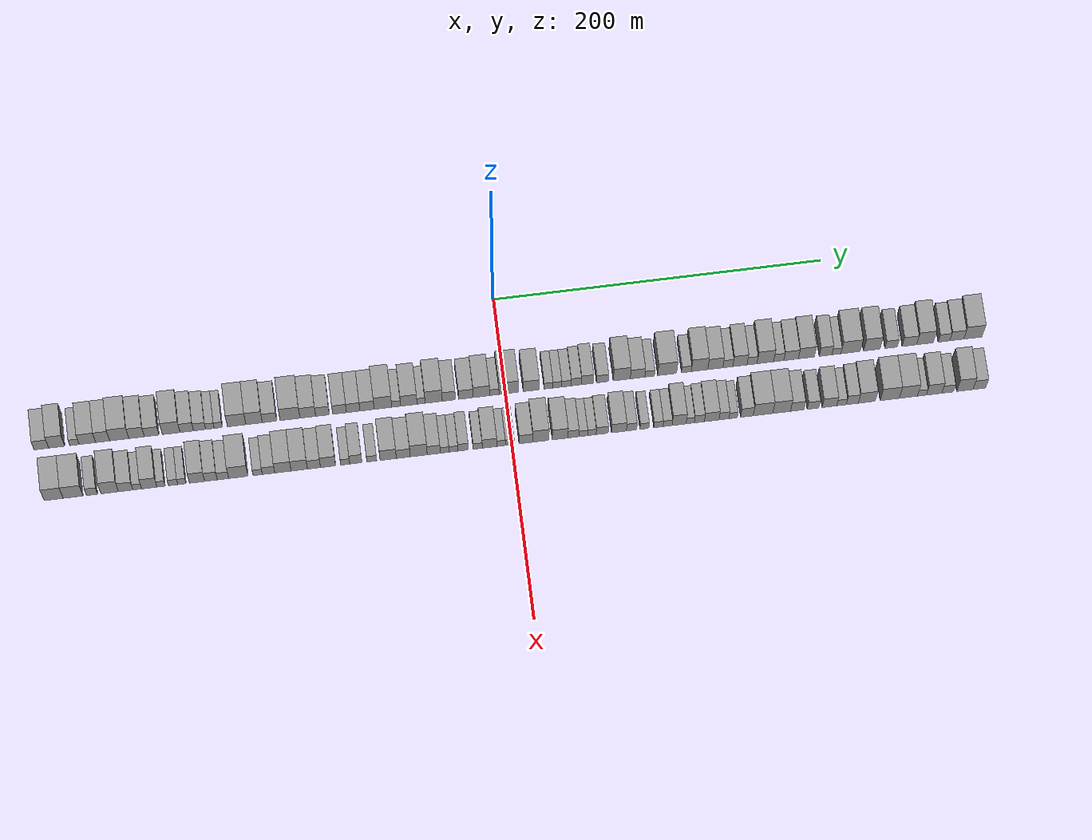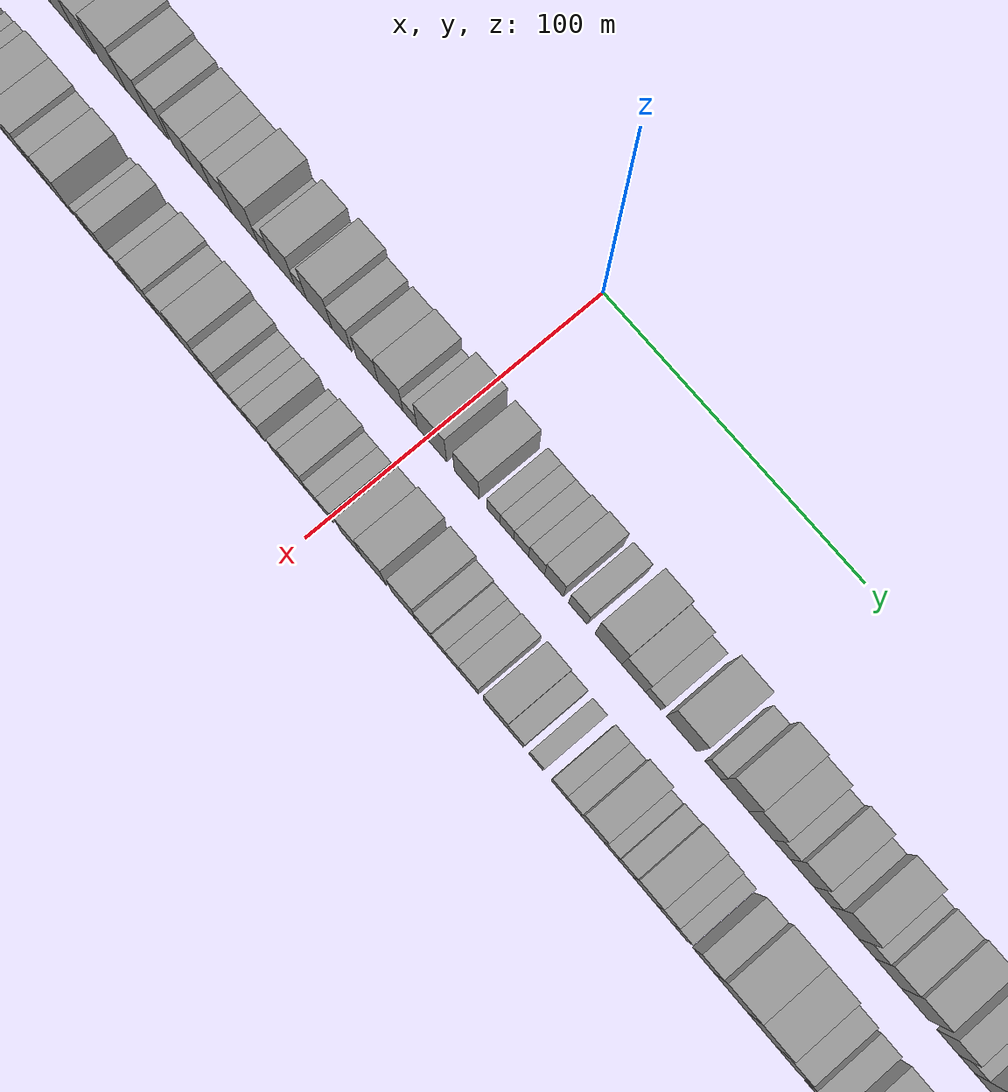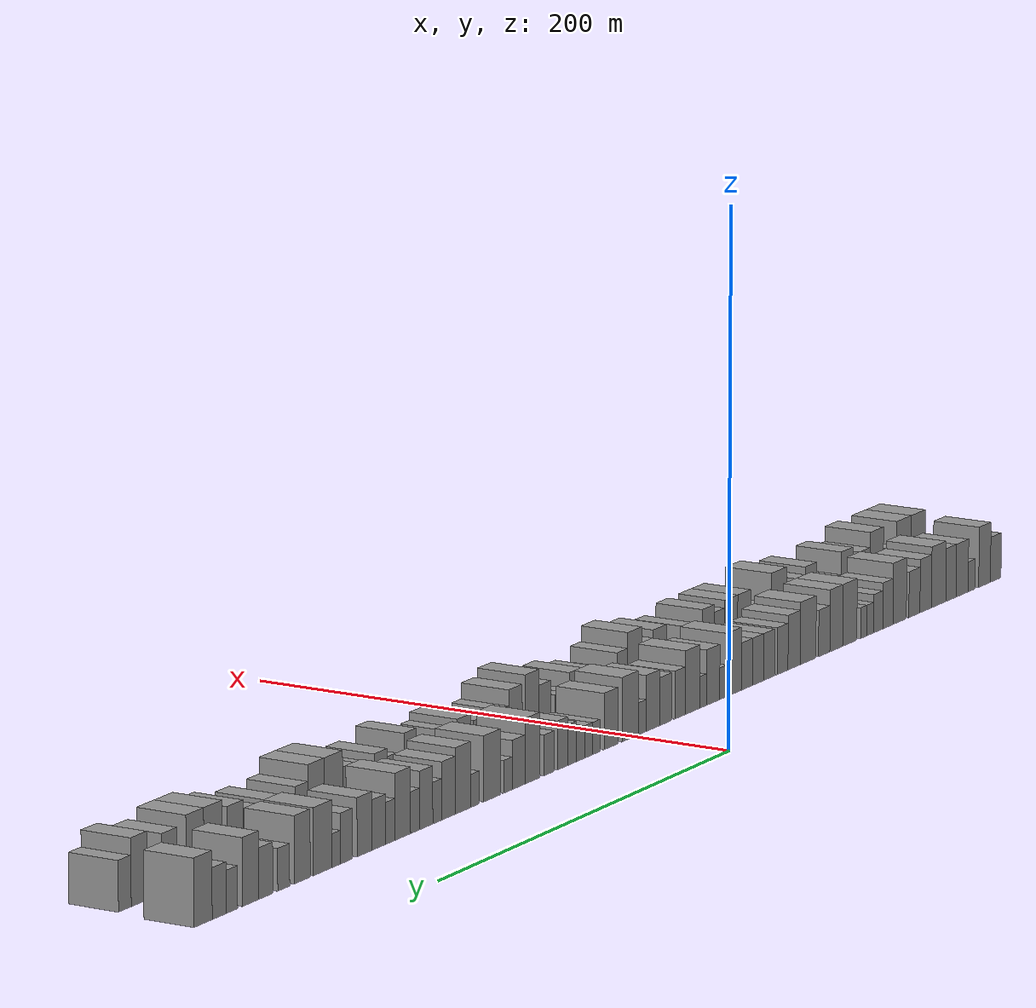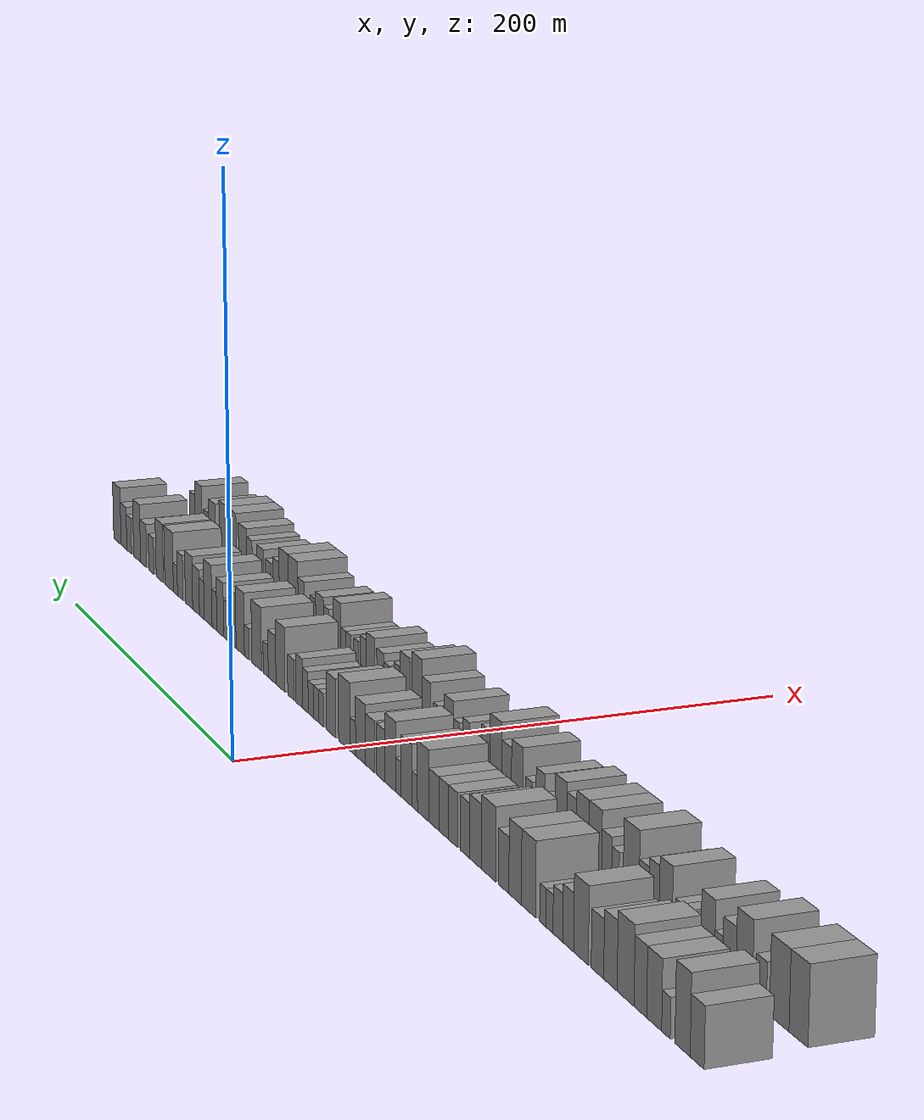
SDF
<sdf version="1.6">
 <world name="default">
  <scene>
   <sky><clouds><speed>12</speed></clouds></sky>
   <ambient>0.4 0.4 0.4 1</ambient>
   <background>0.7 0.7 0.7 1</background>
   <shadows>1</shadows>
  </scene>
  <gravity>0 0 -9.8066</gravity>
  <magnetic_field>6e-06 2.3e-05 -4.2e-05</magnetic_field>
  <physics default="0" name="default_physics" type="ode">
   <ode>
    <solver>
     <type>quick</type>
     <iters>10</iters>
     <sor>1.0</sor>
     <use_dynamic_moi_rescaling>0</use_dynamic_moi_rescaling>
    </solver>
    <constraints>
     <cfm>0</cfm>
     <erp>0.2</erp>
     <contact_max_correcting_vel>100</contact_max_correcting_vel>
     <contact_surface_layer>0.001</contact_surface_layer>
    </constraints>
   </ode>
   <max_step_size>0.004</max_step_size>
   <real_time_factor>1</real_time_factor>
   <real_time_update_rate>250</real_time_update_rate>
  </physics>
  <light name="sun" type="directional">
   <pose>0 0 10 0 0 0</pose>
   <diffuse>0.8 0.8 0.8 1</diffuse>
   <specular>0.2 0.2 0.2 1</specular>
   <attenuation>
    <range>1000</range>
    <constant>0.9</constant>
    <linear>0.01</linear>
    <quadratic>0.001</quadratic>
   </attenuation>
   <direction>-0.5 0.1 -0.9</direction>
  </light>
  <model name="building_1">
   <static>1</static>
   <pose>50.0000 -279.6286 0 0.000000 0.000000 0.000000</pose>
   <link name="link">
    <pose>0 0 9.00 0 0 0</pose>
    <collision name="collision"><geometry><box><size>20.0000 8.7428 18.0000</size></box></geometry></collision>
    <visual name="visual">
     <cast_shadows>0</cast_shadows>
     <geometry><box><size>20.0000 8.7428 18.0000</size></box></geometry>
     <material>
      <script>
       <uri>model://grey_wall/materials/scripts</uri>
       <uri>model://grey_wall/materials/textures</uri>
       <name>vrc/grey_wall</name>
      </script>
     </material>
    </visual>
   </link>
  </model>
  <model name="building_2">
   <static>1</static>
   <pose>50.0000 -270.4098 0 0.000000 0.000000 0.000000</pose>
   <link name="link">
    <pose>0 0 12.00 0 0 0</pose>
    <collision name="collision"><geometry><box><size>20.0000 9.6947 24.0000</size></box></geometry></collision>
    <visual name="visual">
     <cast_shadows>0</cast_shadows>
     <geometry><box><size>20.0000 9.6947 24.0000</size></box></geometry>
     <material>
      <script>
       <uri>model://grey_wall/materials/scripts</uri>
       <uri>model://grey_wall/materials/textures</uri>
       <name>vrc/grey_wall</name>
      </script>
     </material>
    </visual>
   </link>
  </model>
  <model name="building_3">
   <static>1</static>
   <pose>50.0000 -259.7569 0 0.000000 0.000000 0.000000</pose>
   <link name="link">
    <pose>0 0 6.00 0 0 0</pose>
    <collision name="collision"><geometry><box><size>20.0000 5.6109 12.0000</size></box></geometry></collision>
    <visual name="visual">
     <cast_shadows>0</cast_shadows>
     <geometry><box><size>20.0000 5.6109 12.0000</size></box></geometry>
     <material>
      <script>
       <uri>model://grey_wall/materials/scripts</uri>
       <uri>model://grey_wall/materials/textures</uri>
       <name>vrc/grey_wall</name>
      </script>
     </material>
    </visual>
   </link>
  </model>
  <model name="building_4">
   <static>1</static>
   <pose>50.0000 -252.0025 0 0.000000 0.000000 0.000000</pose>
   <link name="link">
    <pose>0 0 10.50 0 0 0</pose>
    <collision name="collision"><geometry><box><size>20.0000 9.8979 21.0000</size></box></geometry></collision>
    <visual name="visual">
     <cast_shadows>0</cast_shadows>
     <geometry><box><size>20.0000 9.8979 21.0000</size></box></geometry>
     <material>
      <script>
       <uri>model://grey_wall/materials/scripts</uri>
       <uri>model://grey_wall/materials/textures</uri>
       <name>vrc/grey_wall</name>
      </script>
     </material>
    </visual>
   </link>
  </model>
  <model name="building_5">
   <static>1</static>
   <pose>50.0000 -242.8396 0 0.000000 0.000000 0.000000</pose>
   <link name="link">
    <pose>0 0 10.50 0 0 0</pose>
    <collision name="collision"><geometry><box><size>20.0000 8.4280 21.0000</size></box></geometry></collision>
    <visual name="visual">
     <cast_shadows>0</cast_shadows>
     <geometry><box><size>20.0000 8.4280 21.0000</size></box></geometry>
     <material>
      <script>
       <uri>model://grey_wall/materials/scripts</uri>
       <uri>model://grey_wall/materials/textures</uri>
       <name>vrc/grey_wall</name>
      </script>
     </material>
    </visual>
   </link>
  </model>
  <model name="building_6">
   <static>1</static>
   <pose>50.0000 -232.8476 0 0.000000 0.000000 0.000000</pose>
   <link name="link">
    <pose>0 0 12.00 0 0 0</pose>
    <collision name="collision"><geometry><box><size>20.0000 11.5561 24.0000</size></box></geometry></collision>
    <visual name="visual">
     <cast_shadows>0</cast_shadows>
     <geometry><box><size>20.0000 11.5561 24.0000</size></box></geometry>
     <material>
      <script>
       <uri>model://grey_wall/materials/scripts</uri>
       <uri>model://grey_wall/materials/textures</uri>
       <name>vrc/grey_wall</name>
      </script>
     </material>
    </visual>
   </link>
  </model>
  <model name="building_7">
   <static>1</static>
   <pose>50.0000 -222.4046 0 0.000000 0.000000 0.000000</pose>
   <link name="link">
    <pose>0 0 10.50 0 0 0</pose>
    <collision name="collision"><geometry><box><size>20.0000 9.3298 21.0000</size></box></geometry></collision>
    <visual name="visual">
     <cast_shadows>0</cast_shadows>
     <geometry><box><size>20.0000 9.3298 21.0000</size></box></geometry>
     <material>
      <script>
       <uri>model://grey_wall/materials/scripts</uri>
       <uri>model://grey_wall/materials/textures</uri>
       <name>vrc/grey_wall</name>
      </script>
     </material>
    </visual>
   </link>
  </model>
  <model name="building_8">
   <static>1</static>
   <pose>50.0000 -213.2914 0 0.000000 0.000000 0.000000</pose>
   <link name="link">
    <pose>0 0 9.00 0 0 0</pose>
    <collision name="collision"><geometry><box><size>20.0000 8.8967 18.0000</size></box></geometry></collision>
    <visual name="visual">
     <cast_shadows>0</cast_shadows>
     <geometry><box><size>20.0000 8.8967 18.0000</size></box></geometry>
     <material>
      <script>
       <uri>model://grey_wall/materials/scripts</uri>
       <uri>model://grey_wall/materials/textures</uri>
       <name>vrc/grey_wall</name>
      </script>
     </material>
    </visual>
   </link>
  </model>
  <model name="building_9">
   <static>1</static>
   <pose>50.0000 -201.5063 0 0.000000 0.000000 0.000000</pose>
   <link name="link">
    <pose>0 0 12.00 0 0 0</pose>
    <collision name="collision"><geometry><box><size>20.0000 10.6734 24.0000</size></box></geometry></collision>
    <visual name="visual">
     <cast_shadows>0</cast_shadows>
     <geometry><box><size>20.0000 10.6734 24.0000</size></box></geometry>
     <material>
      <script>
       <uri>model://grey_wall/materials/scripts</uri>
       <uri>model://grey_wall/materials/textures</uri>
       <name>vrc/grey_wall</name>
      </script>
     </material>
    </visual>
   </link>
  </model>
  <model name="building_10">
   <static>1</static>
   <pose>50.0000 -192.1429 0 0.000000 0.000000 0.000000</pose>
   <link name="link">
    <pose>0 0 9.00 0 0 0</pose>
    <collision name="collision"><geometry><box><size>20.0000 8.0535 18.0000</size></box></geometry></collision>
    <visual name="visual">
     <cast_shadows>0</cast_shadows>
     <geometry><box><size>20.0000 8.0535 18.0000</size></box></geometry>
     <material>
      <script>
       <uri>model://grey_wall/materials/scripts</uri>
       <uri>model://grey_wall/materials/textures</uri>
       <name>vrc/grey_wall</name>
      </script>
     </material>
    </visual>
   </link>
  </model>
  <model name="building_11">
   <static>1</static>
   <pose>50.0000 -184.4632 0 0.000000 0.000000 0.000000</pose>
   <link name="link">
    <pose>0 0 7.50 0 0 0</pose>
    <collision name="collision"><geometry><box><size>20.0000 7.3059 15.0000</size></box></geometry></collision>
    <visual name="visual">
     <cast_shadows>0</cast_shadows>
     <geometry><box><size>20.0000 7.3059 15.0000</size></box></geometry>
     <material>
      <script>
       <uri>model://grey_wall/materials/scripts</uri>
       <uri>model://grey_wall/materials/textures</uri>
       <name>vrc/grey_wall</name>
      </script>
     </material>
    </visual>
   </link>
  </model>
  <model name="building_12">
   <static>1</static>
   <pose>50.0000 -178.2187 0 0.000000 0.000000 0.000000</pose>
   <link name="link">
    <pose>0 0 6.00 0 0 0</pose>
    <collision name="collision"><geometry><box><size>20.0000 5.1832 12.0000</size></box></geometry></collision>
    <visual name="visual">
     <cast_shadows>0</cast_shadows>
     <geometry><box><size>20.0000 5.1832 12.0000</size></box></geometry>
     <material>
      <script>
       <uri>model://grey_wall/materials/scripts</uri>
       <uri>model://grey_wall/materials/textures</uri>
       <name>vrc/grey_wall</name>
      </script>
     </material>
    </visual>
   </link>
  </model>
  <model name="building_13">
   <static>1</static>
   <pose>50.0000 -173.1436 0 0.000000 0.000000 0.000000</pose>
   <link name="link">
    <pose>0 0 6.00 0 0 0</pose>
    <collision name="collision"><geometry><box><size>20.0000 4.9670 12.0000</size></box></geometry></collision>
    <visual name="visual">
     <cast_shadows>0</cast_shadows>
     <geometry><box><size>20.0000 4.9670 12.0000</size></box></geometry>
     <material>
      <script>
       <uri>model://grey_wall/materials/scripts</uri>
       <uri>model://grey_wall/materials/textures</uri>
       <name>vrc/grey_wall</name>
      </script>
     </material>
    </visual>
   </link>
  </model>
  <model name="building_14">
   <static>1</static>
   <pose>50.0000 -162.1004 0 0.000000 0.000000 0.000000</pose>
   <link name="link">
    <pose>0 0 12.00 0 0 0</pose>
    <collision name="collision"><geometry><box><size>20.0000 11.1194 24.0000</size></box></geometry></collision>
    <visual name="visual">
     <cast_shadows>0</cast_shadows>
     <geometry><box><size>20.0000 11.1194 24.0000</size></box></geometry>
     <material>
      <script>
       <uri>model://grey_wall/materials/scripts</uri>
       <uri>model://grey_wall/materials/textures</uri>
       <name>vrc/grey_wall</name>
      </script>
     </material>
    </visual>
   </link>
  </model>
  <model name="building_15">
   <static>1</static>
   <pose>50.0000 -151.5763 0 0.000000 0.000000 0.000000</pose>
   <link name="link">
    <pose>0 0 12.00 0 0 0</pose>
    <collision name="collision"><geometry><box><size>20.0000 9.9287 24.0000</size></box></geometry></collision>
    <visual name="visual">
     <cast_shadows>0</cast_shadows>
     <geometry><box><size>20.0000 9.9287 24.0000</size></box></geometry>
     <material>
      <script>
       <uri>model://grey_wall/materials/scripts</uri>
       <uri>model://grey_wall/materials/textures</uri>
       <name>vrc/grey_wall</name>
      </script>
     </material>
    </visual>
   </link>
  </model>
  <model name="building_16">
   <static>1</static>
   <pose>50.0000 -142.2535 0 0.000000 0.000000 0.000000</pose>
   <link name="link">
    <pose>0 0 9.00 0 0 0</pose>
    <collision name="collision"><geometry><box><size>20.0000 8.7169 18.0000</size></box></geometry></collision>
    <visual name="visual">
     <cast_shadows>0</cast_shadows>
     <geometry><box><size>20.0000 8.7169 18.0000</size></box></geometry>
     <material>
      <script>
       <uri>model://grey_wall/materials/scripts</uri>
       <uri>model://grey_wall/materials/textures</uri>
       <name>vrc/grey_wall</name>
      </script>
     </material>
    </visual>
   </link>
  </model>
  <model name="building_17">
   <static>1</static>
   <pose>50.0000 -129.9366 0 0.000000 0.000000 0.000000</pose>
   <link name="link">
    <pose>0 0 12.00 0 0 0</pose>
    <collision name="collision"><geometry><box><size>20.0000 11.9170 24.0000</size></box></geometry></collision>
    <visual name="visual">
     <cast_shadows>0</cast_shadows>
     <geometry><box><size>20.0000 11.9170 24.0000</size></box></geometry>
     <material>
      <script>
       <uri>model://grey_wall/materials/scripts</uri>
       <uri>model://grey_wall/materials/textures</uri>
       <name>vrc/grey_wall</name>
      </script>
     </material>
    </visual>
   </link>
  </model>
  <model name="building_18">
   <static>1</static>
   <pose>50.0000 -119.2234 0 0.000000 0.000000 0.000000</pose>
   <link name="link">
    <pose>0 0 10.50 0 0 0</pose>
    <collision name="collision"><geometry><box><size>20.0000 9.5093 21.0000</size></box></geometry></collision>
    <visual name="visual">
     <cast_shadows>0</cast_shadows>
     <geometry><box><size>20.0000 9.5093 21.0000</size></box></geometry>
     <material>
      <script>
       <uri>model://grey_wall/materials/scripts</uri>
       <uri>model://grey_wall/materials/textures</uri>
       <name>vrc/grey_wall</name>
      </script>
     </material>
    </visual>
   </link>
  </model>
  <model name="building_19">
   <static>1</static>
   <pose>50.0000 -110.3324 0 0.000000 0.000000 0.000000</pose>
   <link name="link">
    <pose>0 0 9.00 0 0 0</pose>
    <collision name="collision"><geometry><box><size>20.0000 8.2729 18.0000</size></box></geometry></collision>
    <visual name="visual">
     <cast_shadows>0</cast_shadows>
     <geometry><box><size>20.0000 8.2729 18.0000</size></box></geometry>
     <material>
      <script>
       <uri>model://grey_wall/materials/scripts</uri>
       <uri>model://grey_wall/materials/textures</uri>
       <name>vrc/grey_wall</name>
      </script>
     </material>
    </visual>
   </link>
  </model>
  <model name="building_20">
   <static>1</static>
   <pose>50.0000 -100.0319 0 0.000000 0.000000 0.000000</pose>
   <link name="link">
    <pose>0 0 9.00 0 0 0</pose>
    <collision name="collision"><geometry><box><size>20.0000 8.3281 18.0000</size></box></geometry></collision>
    <visual name="visual">
     <cast_shadows>0</cast_shadows>
     <geometry><box><size>20.0000 8.3281 18.0000</size></box></geometry>
     <material>
      <script>
       <uri>model://grey_wall/materials/scripts</uri>
       <uri>model://grey_wall/materials/textures</uri>
       <name>vrc/grey_wall</name>
      </script>
     </material>
    </visual>
   </link>
  </model>
  <model name="building_21">
   <static>1</static>
   <pose>50.0000 -91.8018 0 0.000000 0.000000 0.000000</pose>
   <link name="link">
    <pose>0 0 9.00 0 0 0</pose>
    <collision name="collision"><geometry><box><size>20.0000 8.1321 18.0000</size></box></geometry></collision>
    <visual name="visual">
     <cast_shadows>0</cast_shadows>
     <geometry><box><size>20.0000 8.1321 18.0000</size></box></geometry>
     <material>
      <script>
       <uri>model://grey_wall/materials/scripts</uri>
       <uri>model://grey_wall/materials/textures</uri>
       <name>vrc/grey_wall</name>
      </script>
     </material>
    </visual>
   </link>
  </model>
  <model name="building_22">
   <static>1</static>
   <pose>50.0000 -83.4496 0 0.000000 0.000000 0.000000</pose>
   <link name="link">
    <pose>0 0 9.00 0 0 0</pose>
    <collision name="collision"><geometry><box><size>20.0000 8.5723 18.0000</size></box></geometry></collision>
    <visual name="visual">
     <cast_shadows>0</cast_shadows>
     <geometry><box><size>20.0000 8.5723 18.0000</size></box></geometry>
     <material>
      <script>
       <uri>model://grey_wall/materials/scripts</uri>
       <uri>model://grey_wall/materials/textures</uri>
       <name>vrc/grey_wall</name>
      </script>
     </material>
    </visual>
   </link>
  </model>
  <model name="building_23">
   <static>1</static>
   <pose>50.0000 -73.8428 0 0.000000 0.000000 0.000000</pose>
   <link name="link">
    <pose>0 0 12.00 0 0 0</pose>
    <collision name="collision"><geometry><box><size>20.0000 10.6414 24.0000</size></box></geometry></collision>
    <visual name="visual">
     <cast_shadows>0</cast_shadows>
     <geometry><box><size>20.0000 10.6414 24.0000</size></box></geometry>
     <material>
      <script>
       <uri>model://grey_wall/materials/scripts</uri>
       <uri>model://grey_wall/materials/textures</uri>
       <name>vrc/grey_wall</name>
      </script>
     </material>
    </visual>
   </link>
  </model>
  <model name="building_24">
   <static>1</static>
   <pose>50.0000 -65.8612 0 0.000000 0.000000 0.000000</pose>
   <link name="link">
    <pose>0 0 6.00 0 0 0</pose>
    <collision name="collision"><geometry><box><size>20.0000 5.3218 12.0000</size></box></geometry></collision>
    <visual name="visual">
     <cast_shadows>0</cast_shadows>
     <geometry><box><size>20.0000 5.3218 12.0000</size></box></geometry>
     <material>
      <script>
       <uri>model://grey_wall/materials/scripts</uri>
       <uri>model://grey_wall/materials/textures</uri>
       <name>vrc/grey_wall</name>
      </script>
     </material>
    </visual>
   </link>
  </model>
  <model name="building_25">
   <static>1</static>
   <pose>50.0000 -58.2355 0 0.000000 0.000000 0.000000</pose>
   <link name="link">
    <pose>0 0 10.50 0 0 0</pose>
    <collision name="collision"><geometry><box><size>20.0000 9.9295 21.0000</size></box></geometry></collision>
    <visual name="visual">
     <cast_shadows>0</cast_shadows>
     <geometry><box><size>20.0000 9.9295 21.0000</size></box></geometry>
     <material>
      <script>
       <uri>model://grey_wall/materials/scripts</uri>
       <uri>model://grey_wall/materials/textures</uri>
       <name>vrc/grey_wall</name>
      </script>
     </material>
    </visual>
   </link>
  </model>
  <model name="building_26">
   <static>1</static>
   <pose>50.0000 -50.8598 0 0.000000 0.000000 0.000000</pose>
   <link name="link">
    <pose>0 0 6.00 0 0 0</pose>
    <collision name="collision"><geometry><box><size>20.0000 4.8219 12.0000</size></box></geometry></collision>
    <visual name="visual">
     <cast_shadows>0</cast_shadows>
     <geometry><box><size>20.0000 4.8219 12.0000</size></box></geometry>
     <material>
      <script>
       <uri>model://grey_wall/materials/scripts</uri>
       <uri>model://grey_wall/materials/textures</uri>
       <name>vrc/grey_wall</name>
      </script>
     </material>
    </visual>
   </link>
  </model>
  <model name="building_27">
   <static>1</static>
   <pose>50.0000 -43.2296 0 0.000000 0.000000 0.000000</pose>
   <link name="link">
    <pose>0 0 12.00 0 0 0</pose>
    <collision name="collision"><geometry><box><size>20.0000 10.4385 24.0000</size></box></geometry></collision>
    <visual name="visual">
     <cast_shadows>0</cast_shadows>
     <geometry><box><size>20.0000 10.4385 24.0000</size></box></geometry>
     <material>
      <script>
       <uri>model://grey_wall/materials/scripts</uri>
       <uri>model://grey_wall/materials/textures</uri>
       <name>vrc/grey_wall</name>
      </script>
     </material>
    </visual>
   </link>
  </model>
  <model name="building_28">
   <static>1</static>
   <pose>50.0000 -34.0808 0 0.000000 0.000000 0.000000</pose>
   <link name="link">
    <pose>0 0 9.00 0 0 0</pose>
    <collision name="collision"><geometry><box><size>20.0000 7.8592 18.0000</size></box></geometry></collision>
    <visual name="visual">
     <cast_shadows>0</cast_shadows>
     <geometry><box><size>20.0000 7.8592 18.0000</size></box></geometry>
     <material>
      <script>
       <uri>model://grey_wall/materials/scripts</uri>
       <uri>model://grey_wall/materials/textures</uri>
       <name>vrc/grey_wall</name>
      </script>
     </material>
    </visual>
   </link>
  </model>
  <model name="building_29">
   <static>1</static>
   <pose>50.0000 -23.7560 0 0.000000 0.000000 0.000000</pose>
   <link name="link">
    <pose>0 0 9.00 0 0 0</pose>
    <collision name="collision"><geometry><box><size>20.0000 8.7904 18.0000</size></box></geometry></collision>
    <visual name="visual">
     <cast_shadows>0</cast_shadows>
     <geometry><box><size>20.0000 8.7904 18.0000</size></box></geometry>
     <material>
      <script>
       <uri>model://grey_wall/materials/scripts</uri>
       <uri>model://grey_wall/materials/textures</uri>
       <name>vrc/grey_wall</name>
      </script>
     </material>
    </visual>
   </link>
  </model>
  <model name="building_30">
   <static>1</static>
   <pose>50.0000 -14.3953 0 0.000000 0.000000 0.000000</pose>
   <link name="link">
    <pose>0 0 10.50 0 0 0</pose>
    <collision name="collision"><geometry><box><size>20.0000 9.9312 21.0000</size></box></geometry></collision>
    <visual name="visual">
     <cast_shadows>0</cast_shadows>
     <geometry><box><size>20.0000 9.9312 21.0000</size></box></geometry>
     <material>
      <script>
       <uri>model://grey_wall/materials/scripts</uri>
       <uri>model://grey_wall/materials/textures</uri>
       <name>vrc/grey_wall</name>
      </script>
     </material>
    </visual>
   </link>
  </model>
  <model name="building_31">
   <static>1</static>
   <pose>50.0000 -6.5884 0 0.000000 0.000000 0.000000</pose>
   <link name="link">
    <pose>0 0 6.00 0 0 0</pose>
    <collision name="collision"><geometry><box><size>20.0000 5.6824 12.0000</size></box></geometry></collision>
    <visual name="visual">
     <cast_shadows>0</cast_shadows>
     <geometry><box><size>20.0000 5.6824 12.0000</size></box></geometry>
     <material>
      <script>
       <uri>model://grey_wall/materials/scripts</uri>
       <uri>model://grey_wall/materials/textures</uri>
       <name>vrc/grey_wall</name>
      </script>
     </material>
    </visual>
   </link>
  </model>
  <model name="building_32">
   <static>1</static>
   <pose>50.0000 2.1094 0 0.000000 0.000000 0.000000</pose>
   <link name="link">
    <pose>0 0 12.00 0 0 0</pose>
    <collision name="collision"><geometry><box><size>20.0000 11.7132 24.0000</size></box></geometry></collision>
    <visual name="visual">
     <cast_shadows>0</cast_shadows>
     <geometry><box><size>20.0000 11.7132 24.0000</size></box></geometry>
     <material>
      <script>
       <uri>model://grey_wall/materials/scripts</uri>
       <uri>model://grey_wall/materials/textures</uri>
       <name>vrc/grey_wall</name>
      </script>
     </material>
    </visual>
   </link>
  </model>
  <model name="building_33">
   <static>1</static>
   <pose>50.0000 15.8204 0 0.000000 0.000000 0.000000</pose>
   <link name="link">
    <pose>0 0 10.50 0 0 0</pose>
    <collision name="collision"><geometry><box><size>20.0000 9.7087 21.0000</size></box></geometry></collision>
    <visual name="visual">
     <cast_shadows>0</cast_shadows>
     <geometry><box><size>20.0000 9.7087 21.0000</size></box></geometry>
     <material>
      <script>
       <uri>model://grey_wall/materials/scripts</uri>
       <uri>model://grey_wall/materials/textures</uri>
       <name>vrc/grey_wall</name>
      </script>
     </material>
    </visual>
   </link>
  </model>
  <model name="building_34">
   <static>1</static>
   <pose>50.0000 26.3142 0 0.000000 0.000000 0.000000</pose>
   <link name="link">
    <pose>0 0 6.00 0 0 0</pose>
    <collision name="collision"><geometry><box><size>20.0000 5.2790 12.0000</size></box></geometry></collision>
    <visual name="visual">
     <cast_shadows>0</cast_shadows>
     <geometry><box><size>20.0000 5.2790 12.0000</size></box></geometry>
     <material>
      <script>
       <uri>model://grey_wall/materials/scripts</uri>
       <uri>model://grey_wall/materials/textures</uri>
       <name>vrc/grey_wall</name>
      </script>
     </material>
    </visual>
   </link>
  </model>
  <model name="building_35">
   <static>1</static>
   <pose>50.0000 31.6082 0 0.000000 0.000000 0.000000</pose>
   <link name="link">
    <pose>0 0 6.00 0 0 0</pose>
    <collision name="collision"><geometry><box><size>20.0000 5.3090 12.0000</size></box></geometry></collision>
    <visual name="visual">
     <cast_shadows>0</cast_shadows>
     <geometry><box><size>20.0000 5.3090 12.0000</size></box></geometry>
     <material>
      <script>
       <uri>model://grey_wall/materials/scripts</uri>
       <uri>model://grey_wall/materials/textures</uri>
       <name>vrc/grey_wall</name>
      </script>
     </material>
    </visual>
   </link>
  </model>
  <model name="building_36">
   <static>1</static>
   <pose>50.0000 37.1352 0 0.000000 0.000000 0.000000</pose>
   <link name="link">
    <pose>0 0 6.00 0 0 0</pose>
    <collision name="collision"><geometry><box><size>20.0000 5.7449 12.0000</size></box></geometry></collision>
    <visual name="visual">
     <cast_shadows>0</cast_shadows>
     <geometry><box><size>20.0000 5.7449 12.0000</size></box></geometry>
     <material>
      <script>
       <uri>model://grey_wall/materials/scripts</uri>
       <uri>model://grey_wall/materials/textures</uri>
       <name>vrc/grey_wall</name>
      </script>
     </material>
    </visual>
   </link>
  </model>
  <model name="building_37">
   <static>1</static>
   <pose>50.0000 43.0804 0 0.000000 0.000000 0.000000</pose>
   <link name="link">
    <pose>0 0 7.50 0 0 0</pose>
    <collision name="collision"><geometry><box><size>20.0000 6.1454 15.0000</size></box></geometry></collision>
    <visual name="visual">
     <cast_shadows>0</cast_shadows>
     <geometry><box><size>20.0000 6.1454 15.0000</size></box></geometry>
     <material>
      <script>
       <uri>model://grey_wall/materials/scripts</uri>
       <uri>model://grey_wall/materials/textures</uri>
       <name>vrc/grey_wall</name>
      </script>
     </material>
    </visual>
   </link>
  </model>
  <model name="building_38">
   <static>1</static>
   <pose>50.0000 49.7688 0 0.000000 0.000000 0.000000</pose>
   <link name="link">
    <pose>0 0 9.00 0 0 0</pose>
    <collision name="collision"><geometry><box><size>20.0000 7.2315 18.0000</size></box></geometry></collision>
    <visual name="visual">
     <cast_shadows>0</cast_shadows>
     <geometry><box><size>20.0000 7.2315 18.0000</size></box></geometry>
     <material>
      <script>
       <uri>model://grey_wall/materials/scripts</uri>
       <uri>model://grey_wall/materials/textures</uri>
       <name>vrc/grey_wall</name>
      </script>
     </material>
    </visual>
   </link>
  </model>
  <model name="building_39">
   <static>1</static>
   <pose>50.0000 58.9613 0 0.000000 0.000000 0.000000</pose>
   <link name="link">
    <pose>0 0 7.50 0 0 0</pose>
    <collision name="collision"><geometry><box><size>20.0000 7.1535 15.0000</size></box></geometry></collision>
    <visual name="visual">
     <cast_shadows>0</cast_shadows>
     <geometry><box><size>20.0000 7.1535 15.0000</size></box></geometry>
     <material>
      <script>
       <uri>model://grey_wall/materials/scripts</uri>
       <uri>model://grey_wall/materials/textures</uri>
       <name>vrc/grey_wall</name>
      </script>
     </material>
    </visual>
   </link>
  </model>
  <model name="building_40">
   <static>1</static>
   <pose>50.0000 70.6889 0 0.000000 0.000000 0.000000</pose>
   <link name="link">
    <pose>0 0 12.00 0 0 0</pose>
    <collision name="collision"><geometry><box><size>20.0000 10.3017 24.0000</size></box></geometry></collision>
    <visual name="visual">
     <cast_shadows>0</cast_shadows>
     <geometry><box><size>20.0000 10.3017 24.0000</size></box></geometry>
     <material>
      <script>
       <uri>model://grey_wall/materials/scripts</uri>
       <uri>model://grey_wall/materials/textures</uri>
       <name>vrc/grey_wall</name>
      </script>
     </material>
    </visual>
   </link>
  </model>
  <model name="building_41">
   <static>1</static>
   <pose>50.0000 80.2531 0 0.000000 0.000000 0.000000</pose>
   <link name="link">
    <pose>0 0 9.00 0 0 0</pose>
    <collision name="collision"><geometry><box><size>20.0000 8.8268 18.0000</size></box></geometry></collision>
    <visual name="visual">
     <cast_shadows>0</cast_shadows>
     <geometry><box><size>20.0000 8.8268 18.0000</size></box></geometry>
     <material>
      <script>
       <uri>model://grey_wall/materials/scripts</uri>
       <uri>model://grey_wall/materials/textures</uri>
       <name>vrc/grey_wall</name>
      </script>
     </material>
    </visual>
   </link>
  </model>
  <model name="building_42">
   <static>1</static>
   <pose>50.0000 87.5807 0 0.000000 0.000000 0.000000</pose>
   <link name="link">
    <pose>0 0 6.00 0 0 0</pose>
    <collision name="collision"><geometry><box><size>20.0000 5.8285 12.0000</size></box></geometry></collision>
    <visual name="visual">
     <cast_shadows>0</cast_shadows>
     <geometry><box><size>20.0000 5.8285 12.0000</size></box></geometry>
     <material>
      <script>
       <uri>model://grey_wall/materials/scripts</uri>
       <uri>model://grey_wall/materials/textures</uri>
       <name>vrc/grey_wall</name>
      </script>
     </material>
    </visual>
   </link>
  </model>
  <model name="building_43">
   <static>1</static>
   <pose>50.0000 98.2153 0 0.000000 0.000000 0.000000</pose>
   <link name="link">
    <pose>0 0 12.00 0 0 0</pose>
    <collision name="collision"><geometry><box><size>20.0000 11.4407 24.0000</size></box></geometry></collision>
    <visual name="visual">
     <cast_shadows>0</cast_shadows>
     <geometry><box><size>20.0000 11.4407 24.0000</size></box></geometry>
     <material>
      <script>
       <uri>model://grey_wall/materials/scripts</uri>
       <uri>model://grey_wall/materials/textures</uri>
       <name>vrc/grey_wall</name>
      </script>
     </material>
    </visual>
   </link>
  </model>
  <model name="building_44">
   <static>1</static>
   <pose>50.0000 109.8829 0 0.000000 0.000000 0.000000</pose>
   <link name="link">
    <pose>0 0 6.00 0 0 0</pose>
    <collision name="collision"><geometry><box><size>20.0000 5.8946 12.0000</size></box></geometry></collision>
    <visual name="visual">
     <cast_shadows>0</cast_shadows>
     <geometry><box><size>20.0000 5.8946 12.0000</size></box></geometry>
     <material>
      <script>
       <uri>model://grey_wall/materials/scripts</uri>
       <uri>model://grey_wall/materials/textures</uri>
       <name>vrc/grey_wall</name>
      </script>
     </material>
    </visual>
   </link>
  </model>
  <model name="building_45">
   <static>1</static>
   <pose>50.0000 117.8604 0 0.000000 0.000000 0.000000</pose>
   <link name="link">
    <pose>0 0 12.00 0 0 0</pose>
    <collision name="collision"><geometry><box><size>20.0000 10.0603 24.0000</size></box></geometry></collision>
    <visual name="visual">
     <cast_shadows>0</cast_shadows>
     <geometry><box><size>20.0000 10.0603 24.0000</size></box></geometry>
     <material>
      <script>
       <uri>model://grey_wall/materials/scripts</uri>
       <uri>model://grey_wall/materials/textures</uri>
       <name>vrc/grey_wall</name>
      </script>
     </material>
    </visual>
   </link>
  </model>
  <model name="building_46">
   <static>1</static>
   <pose>50.0000 127.4935 0 0.000000 0.000000 0.000000</pose>
   <link name="link">
    <pose>0 0 10.50 0 0 0</pose>
    <collision name="collision"><geometry><box><size>20.0000 9.2059 21.0000</size></box></geometry></collision>
    <visual name="visual">
     <cast_shadows>0</cast_shadows>
     <geometry><box><size>20.0000 9.2059 21.0000</size></box></geometry>
     <material>
      <script>
       <uri>model://grey_wall/materials/scripts</uri>
       <uri>model://grey_wall/materials/textures</uri>
       <name>vrc/grey_wall</name>
      </script>
     </material>
    </visual>
   </link>
  </model>
  <model name="building_47">
   <static>1</static>
   <pose>50.0000 135.1007 0 0.000000 0.000000 0.000000</pose>
   <link name="link">
    <pose>0 0 7.50 0 0 0</pose>
    <collision name="collision"><geometry><box><size>20.0000 6.0083 15.0000</size></box></geometry></collision>
    <visual name="visual">
     <cast_shadows>0</cast_shadows>
     <geometry><box><size>20.0000 6.0083 15.0000</size></box></geometry>
     <material>
      <script>
       <uri>model://grey_wall/materials/scripts</uri>
       <uri>model://grey_wall/materials/textures</uri>
       <name>vrc/grey_wall</name>
      </script>
     </material>
    </visual>
   </link>
  </model>
  <model name="building_48">
   <static>1</static>
   <pose>50.0000 142.4231 0 0.000000 0.000000 0.000000</pose>
   <link name="link">
    <pose>0 0 10.50 0 0 0</pose>
    <collision name="collision"><geometry><box><size>20.0000 8.6366 21.0000</size></box></geometry></collision>
    <visual name="visual">
     <cast_shadows>0</cast_shadows>
     <geometry><box><size>20.0000 8.6366 21.0000</size></box></geometry>
     <material>
      <script>
       <uri>model://grey_wall/materials/scripts</uri>
       <uri>model://grey_wall/materials/textures</uri>
       <name>vrc/grey_wall</name>
      </script>
     </material>
    </visual>
   </link>
  </model>
  <model name="building_49">
   <static>1</static>
   <pose>50.0000 149.7621 0 0.000000 0.000000 0.000000</pose>
   <link name="link">
    <pose>0 0 7.50 0 0 0</pose>
    <collision name="collision"><geometry><box><size>20.0000 6.0415 15.0000</size></box></geometry></collision>
    <visual name="visual">
     <cast_shadows>0</cast_shadows>
     <geometry><box><size>20.0000 6.0415 15.0000</size></box></geometry>
     <material>
      <script>
       <uri>model://grey_wall/materials/scripts</uri>
       <uri>model://grey_wall/materials/textures</uri>
       <name>vrc/grey_wall</name>
      </script>
     </material>
    </visual>
   </link>
  </model>
  <model name="building_50">
   <static>1</static>
   <pose>50.0000 157.8326 0 0.000000 0.000000 0.000000</pose>
   <link name="link">
    <pose>0 0 12.00 0 0 0</pose>
    <collision name="collision"><geometry><box><size>20.0000 10.0995 24.0000</size></box></geometry></collision>
    <visual name="visual">
     <cast_shadows>0</cast_shadows>
     <geometry><box><size>20.0000 10.0995 24.0000</size></box></geometry>
     <material>
      <script>
       <uri>model://grey_wall/materials/scripts</uri>
       <uri>model://grey_wall/materials/textures</uri>
       <name>vrc/grey_wall</name>
      </script>
     </material>
    </visual>
   </link>
  </model>
  <model name="building_51">
   <static>1</static>
   <pose>50.0000 165.9687 0 0.000000 0.000000 0.000000</pose>
   <link name="link">
    <pose>0 0 7.50 0 0 0</pose>
    <collision name="collision"><geometry><box><size>20.0000 6.1727 15.0000</size></box></geometry></collision>
    <visual name="visual">
     <cast_shadows>0</cast_shadows>
     <geometry><box><size>20.0000 6.1727 15.0000</size></box></geometry>
     <material>
      <script>
       <uri>model://grey_wall/materials/scripts</uri>
       <uri>model://grey_wall/materials/textures</uri>
       <name>vrc/grey_wall</name>
      </script>
     </material>
    </visual>
   </link>
  </model>
  <model name="building_52">
   <static>1</static>
   <pose>50.0000 173.4965 0 0.000000 0.000000 0.000000</pose>
   <link name="link">
    <pose>0 0 9.00 0 0 0</pose>
    <collision name="collision"><geometry><box><size>20.0000 8.8830 18.0000</size></box></geometry></collision>
    <visual name="visual">
     <cast_shadows>0</cast_shadows>
     <geometry><box><size>20.0000 8.8830 18.0000</size></box></geometry>
     <material>
      <script>
       <uri>model://grey_wall/materials/scripts</uri>
       <uri>model://grey_wall/materials/textures</uri>
       <name>vrc/grey_wall</name>
      </script>
     </material>
    </visual>
   </link>
  </model>
  <model name="building_53">
   <static>1</static>
   <pose>50.0000 182.7854 0 0.000000 0.000000 0.000000</pose>
   <link name="link">
    <pose>0 0 10.50 0 0 0</pose>
    <collision name="collision"><geometry><box><size>20.0000 9.6948 21.0000</size></box></geometry></collision>
    <visual name="visual">
     <cast_shadows>0</cast_shadows>
     <geometry><box><size>20.0000 9.6948 21.0000</size></box></geometry>
     <material>
      <script>
       <uri>model://grey_wall/materials/scripts</uri>
       <uri>model://grey_wall/materials/textures</uri>
       <name>vrc/grey_wall</name>
      </script>
     </material>
    </visual>
   </link>
  </model>
  <model name="building_54">
   <static>1</static>
   <pose>50.0000 194.4416 0 0.000000 0.000000 0.000000</pose>
   <link name="link">
    <pose>0 0 9.00 0 0 0</pose>
    <collision name="collision"><geometry><box><size>20.0000 7.6175 18.0000</size></box></geometry></collision>
    <visual name="visual">
     <cast_shadows>0</cast_shadows>
     <geometry><box><size>20.0000 7.6175 18.0000</size></box></geometry>
     <material>
      <script>
       <uri>model://grey_wall/materials/scripts</uri>
       <uri>model://grey_wall/materials/textures</uri>
       <name>vrc/grey_wall</name>
      </script>
     </material>
    </visual>
   </link>
  </model>
  <model name="building_55">
   <static>1</static>
   <pose>50.0000 201.0406 0 0.000000 0.000000 0.000000</pose>
   <link name="link">
    <pose>0 0 6.00 0 0 0</pose>
    <collision name="collision"><geometry><box><size>20.0000 5.5805 12.0000</size></box></geometry></collision>
    <visual name="visual">
     <cast_shadows>0</cast_shadows>
     <geometry><box><size>20.0000 5.5805 12.0000</size></box></geometry>
     <material>
      <script>
       <uri>model://grey_wall/materials/scripts</uri>
       <uri>model://grey_wall/materials/textures</uri>
       <name>vrc/grey_wall</name>
      </script>
     </material>
    </visual>
   </link>
  </model>
  <model name="building_56">
   <static>1</static>
   <pose>50.0000 209.7148 0 0.000000 0.000000 0.000000</pose>
   <link name="link">
    <pose>0 0 12.00 0 0 0</pose>
    <collision name="collision"><geometry><box><size>20.0000 11.7679 24.0000</size></box></geometry></collision>
    <visual name="visual">
     <cast_shadows>0</cast_shadows>
     <geometry><box><size>20.0000 11.7679 24.0000</size></box></geometry>
     <material>
      <script>
       <uri>model://grey_wall/materials/scripts</uri>
       <uri>model://grey_wall/materials/textures</uri>
       <name>vrc/grey_wall</name>
      </script>
     </material>
    </visual>
   </link>
  </model>
  <model name="building_57">
   <static>1</static>
   <pose>50.0000 222.6234 0 0.000000 0.000000 0.000000</pose>
   <link name="link">
    <pose>0 0 12.00 0 0 0</pose>
    <collision name="collision"><geometry><box><size>20.0000 10.0494 24.0000</size></box></geometry></collision>
    <visual name="visual">
     <cast_shadows>0</cast_shadows>
     <geometry><box><size>20.0000 10.0494 24.0000</size></box></geometry>
     <material>
      <script>
       <uri>model://grey_wall/materials/scripts</uri>
       <uri>model://grey_wall/materials/textures</uri>
       <name>vrc/grey_wall</name>
      </script>
     </material>
    </visual>
   </link>
  </model>
  <model name="building_58">
   <static>1</static>
   <pose>50.0000 234.3908 0 0.000000 0.000000 0.000000</pose>
   <link name="link">
    <pose>0 0 7.50 0 0 0</pose>
    <collision name="collision"><geometry><box><size>20.0000 7.4855 15.0000</size></box></geometry></collision>
    <visual name="visual">
     <cast_shadows>0</cast_shadows>
     <geometry><box><size>20.0000 7.4855 15.0000</size></box></geometry>
     <material>
      <script>
       <uri>model://grey_wall/materials/scripts</uri>
       <uri>model://grey_wall/materials/textures</uri>
       <name>vrc/grey_wall</name>
      </script>
     </material>
    </visual>
   </link>
  </model>
  <model name="building_59">
   <static>1</static>
   <pose>50.0000 245.5491 0 0.000000 0.000000 0.000000</pose>
   <link name="link">
    <pose>0 0 9.00 0 0 0</pose>
    <collision name="collision"><geometry><box><size>20.0000 8.8310 18.0000</size></box></geometry></collision>
    <visual name="visual">
     <cast_shadows>0</cast_shadows>
     <geometry><box><size>20.0000 8.8310 18.0000</size></box></geometry>
     <material>
      <script>
       <uri>model://grey_wall/materials/scripts</uri>
       <uri>model://grey_wall/materials/textures</uri>
       <name>vrc/grey_wall</name>
      </script>
     </material>
    </visual>
   </link>
  </model>
  <model name="building_60">
   <static>1</static>
   <pose>50.0000 255.0190 0 0.000000 0.000000 0.000000</pose>
   <link name="link">
    <pose>0 0 12.00 0 0 0</pose>
    <collision name="collision"><geometry><box><size>20.0000 10.1087 24.0000</size></box></geometry></collision>
    <visual name="visual">
     <cast_shadows>0</cast_shadows>
     <geometry><box><size>20.0000 10.1087 24.0000</size></box></geometry>
     <material>
      <script>
       <uri>model://grey_wall/materials/scripts</uri>
       <uri>model://grey_wall/materials/textures</uri>
       <name>vrc/grey_wall</name>
      </script>
     </material>
    </visual>
   </link>
  </model>
  <model name="building_61">
   <static>1</static>
   <pose>50.0000 266.5983 0 0.000000 0.000000 0.000000</pose>
   <link name="link">
    <pose>0 0 7.50 0 0 0</pose>
    <collision name="collision"><geometry><box><size>20.0000 7.0500 15.0000</size></box></geometry></collision>
    <visual name="visual">
     <cast_shadows>0</cast_shadows>
     <geometry><box><size>20.0000 7.0500 15.0000</size></box></geometry>
     <material>
      <script>
       <uri>model://grey_wall/materials/scripts</uri>
       <uri>model://grey_wall/materials/textures</uri>
       <name>vrc/grey_wall</name>
      </script>
     </material>
    </visual>
   </link>
  </model>
  <model name="building_62">
   <static>1</static>
   <pose>50.0000 274.4224 0 0.000000 0.000000 0.000000</pose>
   <link name="link">
    <pose>0 0 9.00 0 0 0</pose>
    <collision name="collision"><geometry><box><size>20.0000 8.5982 18.0000</size></box></geometry></collision>
    <visual name="visual">
     <cast_shadows>0</cast_shadows>
     <geometry><box><size>20.0000 8.5982 18.0000</size></box></geometry>
     <material>
      <script>
       <uri>model://grey_wall/materials/scripts</uri>
       <uri>model://grey_wall/materials/textures</uri>
       <name>vrc/grey_wall</name>
      </script>
     </material>
    </visual>
   </link>
  </model>
  <model name="building_63">
   <static>1</static>
   <pose>50.0000 284.2495 0 0.000000 0.000000 0.000000</pose>
   <link name="link">
    <pose>0 0 12.00 0 0 0</pose>
    <collision name="collision"><geometry><box><size>20.0000 11.0559 24.0000</size></box></geometry></collision>
    <visual name="visual">
     <cast_shadows>0</cast_shadows>
     <geometry><box><size>20.0000 11.0559 24.0000</size></box></geometry>
     <material>
      <script>
       <uri>model://grey_wall/materials/scripts</uri>
       <uri>model://grey_wall/materials/textures</uri>
       <name>vrc/grey_wall</name>
      </script>
     </material>
    </visual>
   </link>
  </model>
  <model name="building_64">
   <static>1</static>
   <pose>82.0000 -275.2955 0 0.000000 0.000000 0.000000</pose>
   <link name="link">
    <pose>0 0 12.00 0 0 0</pose>
    <collision name="collision"><geometry><box><size>20.0000 11.4089 24.0000</size></box></geometry></collision>
    <visual name="visual">
     <cast_shadows>0</cast_shadows>
     <geometry><box><size>20.0000 11.4089 24.0000</size></box></geometry>
     <material>
      <script>
       <uri>model://grey_wall/materials/scripts</uri>
       <uri>model://grey_wall/materials/textures</uri>
       <name>vrc/grey_wall</name>
      </script>
     </material>
    </visual>
   </link>
  </model>
  <model name="building_65">
   <static>1</static>
   <pose>82.0000 -263.6320 0 0.000000 0.000000 0.000000</pose>
   <link name="link">
    <pose>0 0 12.00 0 0 0</pose>
    <collision name="collision"><geometry><box><size>20.0000 11.9181 24.0000</size></box></geometry></collision>
    <visual name="visual">
     <cast_shadows>0</cast_shadows>
     <geometry><box><size>20.0000 11.9181 24.0000</size></box></geometry>
     <material>
      <script>
       <uri>model://grey_wall/materials/scripts</uri>
       <uri>model://grey_wall/materials/textures</uri>
       <name>vrc/grey_wall</name>
      </script>
     </material>
    </visual>
   </link>
  </model>
  <model name="building_66">
   <static>1</static>
   <pose>82.0000 -252.3101 0 0.000000 0.000000 0.000000</pose>
   <link name="link">
    <pose>0 0 7.50 0 0 0</pose>
    <collision name="collision"><geometry><box><size>20.0000 6.7258 15.0000</size></box></geometry></collision>
    <visual name="visual">
     <cast_shadows>0</cast_shadows>
     <geometry><box><size>20.0000 6.7258 15.0000</size></box></geometry>
     <material>
      <script>
       <uri>model://grey_wall/materials/scripts</uri>
       <uri>model://grey_wall/materials/textures</uri>
       <name>vrc/grey_wall</name>
      </script>
     </material>
    </visual>
   </link>
  </model>
  <model name="building_67">
   <static>1</static>
   <pose>82.0000 -241.6834 0 0.000000 0.000000 0.000000</pose>
   <link name="link">
    <pose>0 0 12.00 0 0 0</pose>
    <collision name="collision"><geometry><box><size>20.0000 10.5275 24.0000</size></box></geometry></collision>
    <visual name="visual">
     <cast_shadows>0</cast_shadows>
     <geometry><box><size>20.0000 10.5275 24.0000</size></box></geometry>
     <material>
      <script>
       <uri>model://grey_wall/materials/scripts</uri>
       <uri>model://grey_wall/materials/textures</uri>
       <name>vrc/grey_wall</name>
      </script>
     </material>
    </visual>
   </link>
  </model>
  <model name="building_68">
   <static>1</static>
   <pose>82.0000 -232.1218 0 0.000000 0.000000 0.000000</pose>
   <link name="link">
    <pose>0 0 9.00 0 0 0</pose>
    <collision name="collision"><geometry><box><size>20.0000 8.5956 18.0000</size></box></geometry></collision>
    <visual name="visual">
     <cast_shadows>0</cast_shadows>
     <geometry><box><size>20.0000 8.5956 18.0000</size></box></geometry>
     <material>
      <script>
       <uri>model://grey_wall/materials/scripts</uri>
       <uri>model://grey_wall/materials/textures</uri>
       <name>vrc/grey_wall</name>
      </script>
     </material>
    </visual>
   </link>
  </model>
  <model name="building_69">
   <static>1</static>
   <pose>82.0000 -225.1741 0 0.000000 0.000000 0.000000</pose>
   <link name="link">
    <pose>0 0 6.00 0 0 0</pose>
    <collision name="collision"><geometry><box><size>20.0000 5.2998 12.0000</size></box></geometry></collision>
    <visual name="visual">
     <cast_shadows>0</cast_shadows>
     <geometry><box><size>20.0000 5.2998 12.0000</size></box></geometry>
     <material>
      <script>
       <uri>model://grey_wall/materials/scripts</uri>
       <uri>model://grey_wall/materials/textures</uri>
       <name>vrc/grey_wall</name>
      </script>
     </material>
    </visual>
   </link>
  </model>
  <model name="building_70">
   <static>1</static>
   <pose>82.0000 -217.9201 0 0.000000 0.000000 0.000000</pose>
   <link name="link">
    <pose>0 0 10.50 0 0 0</pose>
    <collision name="collision"><geometry><box><size>20.0000 9.2083 21.0000</size></box></geometry></collision>
    <visual name="visual">
     <cast_shadows>0</cast_shadows>
     <geometry><box><size>20.0000 9.2083 21.0000</size></box></geometry>
     <material>
      <script>
       <uri>model://grey_wall/materials/scripts</uri>
       <uri>model://grey_wall/materials/textures</uri>
       <name>vrc/grey_wall</name>
      </script>
     </material>
    </visual>
   </link>
  </model>
  <model name="building_71">
   <static>1</static>
   <pose>82.0000 -210.8605 0 0.000000 0.000000 0.000000</pose>
   <link name="link">
    <pose>0 0 6.00 0 0 0</pose>
    <collision name="collision"><geometry><box><size>20.0000 4.9110 12.0000</size></box></geometry></collision>
    <visual name="visual">
     <cast_shadows>0</cast_shadows>
     <geometry><box><size>20.0000 4.9110 12.0000</size></box></geometry>
     <material>
      <script>
       <uri>model://grey_wall/materials/scripts</uri>
       <uri>model://grey_wall/materials/textures</uri>
       <name>vrc/grey_wall</name>
      </script>
     </material>
    </visual>
   </link>
  </model>
  <model name="building_72">
   <static>1</static>
   <pose>82.0000 -203.6284 0 0.000000 0.000000 0.000000</pose>
   <link name="link">
    <pose>0 0 6.00 0 0 0</pose>
    <collision name="collision"><geometry><box><size>20.0000 5.5532 12.0000</size></box></geometry></collision>
    <visual name="visual">
     <cast_shadows>0</cast_shadows>
     <geometry><box><size>20.0000 5.5532 12.0000</size></box></geometry>
     <material>
      <script>
       <uri>model://grey_wall/materials/scripts</uri>
       <uri>model://grey_wall/materials/textures</uri>
       <name>vrc/grey_wall</name>
      </script>
     </material>
    </visual>
   </link>
  </model>
  <model name="building_73">
   <static>1</static>
   <pose>82.0000 -198.3500 0 0.000000 0.000000 0.000000</pose>
   <link name="link">
    <pose>0 0 6.00 0 0 0</pose>
    <collision name="collision"><geometry><box><size>20.0000 5.0036 12.0000</size></box></geometry></collision>
    <visual name="visual">
     <cast_shadows>0</cast_shadows>
     <geometry><box><size>20.0000 5.0036 12.0000</size></box></geometry>
     <material>
      <script>
       <uri>model://grey_wall/materials/scripts</uri>
       <uri>model://grey_wall/materials/textures</uri>
       <name>vrc/grey_wall</name>
      </script>
     </material>
    </visual>
   </link>
  </model>
  <model name="building_74">
   <static>1</static>
   <pose>82.0000 -189.2914 0 0.000000 0.000000 0.000000</pose>
   <link name="link">
    <pose>0 0 10.50 0 0 0</pose>
    <collision name="collision"><geometry><box><size>20.0000 9.1135 21.0000</size></box></geometry></collision>
    <visual name="visual">
     <cast_shadows>0</cast_shadows>
     <geometry><box><size>20.0000 9.1135 21.0000</size></box></geometry>
     <material>
      <script>
       <uri>model://grey_wall/materials/scripts</uri>
       <uri>model://grey_wall/materials/textures</uri>
       <name>vrc/grey_wall</name>
      </script>
     </material>
    </visual>
   </link>
  </model>
  <model name="building_75">
   <static>1</static>
   <pose>82.0000 -180.9517 0 0.000000 0.000000 0.000000</pose>
   <link name="link">
    <pose>0 0 9.00 0 0 0</pose>
    <collision name="collision"><geometry><box><size>20.0000 7.5658 18.0000</size></box></geometry></collision>
    <visual name="visual">
     <cast_shadows>0</cast_shadows>
     <geometry><box><size>20.0000 7.5658 18.0000</size></box></geometry>
     <material>
      <script>
       <uri>model://grey_wall/materials/scripts</uri>
       <uri>model://grey_wall/materials/textures</uri>
       <name>vrc/grey_wall</name>
      </script>
     </material>
    </visual>
   </link>
  </model>
  <model name="building_76">
   <static>1</static>
   <pose>82.0000 -173.7455 0 0.000000 0.000000 0.000000</pose>
   <link name="link">
    <pose>0 0 7.50 0 0 0</pose>
    <collision name="collision"><geometry><box><size>20.0000 6.8468 15.0000</size></box></geometry></collision>
    <visual name="visual">
     <cast_shadows>0</cast_shadows>
     <geometry><box><size>20.0000 6.8468 15.0000</size></box></geometry>
     <material>
      <script>
       <uri>model://grey_wall/materials/scripts</uri>
       <uri>model://grey_wall/materials/textures</uri>
       <name>vrc/grey_wall</name>
      </script>
     </material>
    </visual>
   </link>
  </model>
  <model name="building_77">
   <static>1</static>
   <pose>82.0000 -164.4820 0 0.000000 0.000000 0.000000</pose>
   <link name="link">
    <pose>0 0 12.00 0 0 0</pose>
    <collision name="collision"><geometry><box><size>20.0000 11.6801 24.0000</size></box></geometry></collision>
    <visual name="visual">
     <cast_shadows>0</cast_shadows>
     <geometry><box><size>20.0000 11.6801 24.0000</size></box></geometry>
     <material>
      <script>
       <uri>model://grey_wall/materials/scripts</uri>
       <uri>model://grey_wall/materials/textures</uri>
       <name>vrc/grey_wall</name>
      </script>
     </material>
    </visual>
   </link>
  </model>
  <model name="building_78">
   <static>1</static>
   <pose>82.0000 -152.8431 0 0.000000 0.000000 0.000000</pose>
   <link name="link">
    <pose>0 0 6.00 0 0 0</pose>
    <collision name="collision"><geometry><box><size>20.0000 5.5977 12.0000</size></box></geometry></collision>
    <visual name="visual">
     <cast_shadows>0</cast_shadows>
     <geometry><box><size>20.0000 5.5977 12.0000</size></box></geometry>
     <material>
      <script>
       <uri>model://grey_wall/materials/scripts</uri>
       <uri>model://grey_wall/materials/textures</uri>
       <name>vrc/grey_wall</name>
      </script>
     </material>
    </visual>
   </link>
  </model>
  <model name="building_79">
   <static>1</static>
   <pose>82.0000 -146.3173 0 0.000000 0.000000 0.000000</pose>
   <link name="link">
    <pose>0 0 7.50 0 0 0</pose>
    <collision name="collision"><geometry><box><size>20.0000 7.4538 15.0000</size></box></geometry></collision>
    <visual name="visual">
     <cast_shadows>0</cast_shadows>
     <geometry><box><size>20.0000 7.4538 15.0000</size></box></geometry>
     <material>
      <script>
       <uri>model://grey_wall/materials/scripts</uri>
       <uri>model://grey_wall/materials/textures</uri>
       <name>vrc/grey_wall</name>
      </script>
     </material>
    </visual>
   </link>
  </model>
  <model name="building_80">
   <static>1</static>
   <pose>82.0000 -137.6907 0 0.000000 0.000000 0.000000</pose>
   <link name="link">
    <pose>0 0 10.50 0 0 0</pose>
    <collision name="collision"><geometry><box><size>20.0000 9.7994 21.0000</size></box></geometry></collision>
    <visual name="visual">
     <cast_shadows>0</cast_shadows>
     <geometry><box><size>20.0000 9.7994 21.0000</size></box></geometry>
     <material>
      <script>
       <uri>model://grey_wall/materials/scripts</uri>
       <uri>model://grey_wall/materials/textures</uri>
       <name>vrc/grey_wall</name>
      </script>
     </material>
    </visual>
   </link>
  </model>
  <model name="building_81">
   <static>1</static>
   <pose>82.0000 -127.8732 0 0.000000 0.000000 0.000000</pose>
   <link name="link">
    <pose>0 0 10.50 0 0 0</pose>
    <collision name="collision"><geometry><box><size>20.0000 9.8355 21.0000</size></box></geometry></collision>
    <visual name="visual">
     <cast_shadows>0</cast_shadows>
     <geometry><box><size>20.0000 9.8355 21.0000</size></box></geometry>
     <material>
      <script>
       <uri>model://grey_wall/materials/scripts</uri>
       <uri>model://grey_wall/materials/textures</uri>
       <name>vrc/grey_wall</name>
      </script>
     </material>
    </visual>
   </link>
  </model>
  <model name="building_82">
   <static>1</static>
   <pose>82.0000 -119.0408 0 0.000000 0.000000 0.000000</pose>
   <link name="link">
    <pose>0 0 9.00 0 0 0</pose>
    <collision name="collision"><geometry><box><size>20.0000 7.8293 18.0000</size></box></geometry></collision>
    <visual name="visual">
     <cast_shadows>0</cast_shadows>
     <geometry><box><size>20.0000 7.8293 18.0000</size></box></geometry>
     <material>
      <script>
       <uri>model://grey_wall/materials/scripts</uri>
       <uri>model://grey_wall/materials/textures</uri>
       <name>vrc/grey_wall</name>
      </script>
     </material>
    </visual>
   </link>
  </model>
  <model name="building_83">
   <static>1</static>
   <pose>82.0000 -110.5691 0 0.000000 0.000000 0.000000</pose>
   <link name="link">
    <pose>0 0 10.50 0 0 0</pose>
    <collision name="collision"><geometry><box><size>20.0000 9.1142 21.0000</size></box></geometry></collision>
    <visual name="visual">
     <cast_shadows>0</cast_shadows>
     <geometry><box><size>20.0000 9.1142 21.0000</size></box></geometry>
     <material>
      <script>
       <uri>model://grey_wall/materials/scripts</uri>
       <uri>model://grey_wall/materials/textures</uri>
       <name>vrc/grey_wall</name>
      </script>
     </material>
    </visual>
   </link>
  </model>
  <model name="building_84">
   <static>1</static>
   <pose>82.0000 -100.2811 0 0.000000 0.000000 0.000000</pose>
   <link name="link">
    <pose>0 0 6.00 0 0 0</pose>
    <collision name="collision"><geometry><box><size>20.0000 5.4619 12.0000</size></box></geometry></collision>
    <visual name="visual">
     <cast_shadows>0</cast_shadows>
     <geometry><box><size>20.0000 5.4619 12.0000</size></box></geometry>
     <material>
      <script>
       <uri>model://grey_wall/materials/scripts</uri>
       <uri>model://grey_wall/materials/textures</uri>
       <name>vrc/grey_wall</name>
      </script>
     </material>
    </visual>
   </link>
  </model>
  <model name="building_85">
   <static>1</static>
   <pose>82.0000 -93.8943 0 0.000000 0.000000 0.000000</pose>
   <link name="link">
    <pose>0 0 9.00 0 0 0</pose>
    <collision name="collision"><geometry><box><size>20.0000 7.3117 18.0000</size></box></geometry></collision>
    <visual name="visual">
     <cast_shadows>0</cast_shadows>
     <geometry><box><size>20.0000 7.3117 18.0000</size></box></geometry>
     <material>
      <script>
       <uri>model://grey_wall/materials/scripts</uri>
       <uri>model://grey_wall/materials/textures</uri>
       <name>vrc/grey_wall</name>
      </script>
     </material>
    </visual>
   </link>
  </model>
  <model name="building_86">
   <static>1</static>
   <pose>82.0000 -84.2694 0 0.000000 0.000000 0.000000</pose>
   <link name="link">
    <pose>0 0 6.00 0 0 0</pose>
    <collision name="collision"><geometry><box><size>20.0000 5.9382 12.0000</size></box></geometry></collision>
    <visual name="visual">
     <cast_shadows>0</cast_shadows>
     <geometry><box><size>20.0000 5.9382 12.0000</size></box></geometry>
     <material>
      <script>
       <uri>model://grey_wall/materials/scripts</uri>
       <uri>model://grey_wall/materials/textures</uri>
       <name>vrc/grey_wall</name>
      </script>
     </material>
    </visual>
   </link>
  </model>
  <model name="building_87">
   <static>1</static>
   <pose>82.0000 -74.4028 0 0.000000 0.000000 0.000000</pose>
   <link name="link">
    <pose>0 0 10.50 0 0 0</pose>
    <collision name="collision"><geometry><box><size>20.0000 9.7950 21.0000</size></box></geometry></collision>
    <visual name="visual">
     <cast_shadows>0</cast_shadows>
     <geometry><box><size>20.0000 9.7950 21.0000</size></box></geometry>
     <material>
      <script>
       <uri>model://grey_wall/materials/scripts</uri>
       <uri>model://grey_wall/materials/textures</uri>
       <name>vrc/grey_wall</name>
      </script>
     </material>
    </visual>
   </link>
  </model>
  <model name="building_88">
   <static>1</static>
   <pose>82.0000 -65.3342 0 0.000000 0.000000 0.000000</pose>
   <link name="link">
    <pose>0 0 9.00 0 0 0</pose>
    <collision name="collision"><geometry><box><size>20.0000 8.3422 18.0000</size></box></geometry></collision>
    <visual name="visual">
     <cast_shadows>0</cast_shadows>
     <geometry><box><size>20.0000 8.3422 18.0000</size></box></geometry>
     <material>
      <script>
       <uri>model://grey_wall/materials/scripts</uri>
       <uri>model://grey_wall/materials/textures</uri>
       <name>vrc/grey_wall</name>
      </script>
     </material>
    </visual>
   </link>
  </model>
  <model name="building_89">
   <static>1</static>
   <pose>82.0000 -56.0414 0 0.000000 0.000000 0.000000</pose>
   <link name="link">
    <pose>0 0 12.00 0 0 0</pose>
    <collision name="collision"><geometry><box><size>20.0000 10.2433 24.0000</size></box></geometry></collision>
    <visual name="visual">
     <cast_shadows>0</cast_shadows>
     <geometry><box><size>20.0000 10.2433 24.0000</size></box></geometry>
     <material>
      <script>
       <uri>model://grey_wall/materials/scripts</uri>
       <uri>model://grey_wall/materials/textures</uri>
       <name>vrc/grey_wall</name>
      </script>
     </material>
    </visual>
   </link>
  </model>
  <model name="building_90">
   <static>1</static>
   <pose>82.0000 -46.9925 0 0.000000 0.000000 0.000000</pose>
   <link name="link">
    <pose>0 0 9.00 0 0 0</pose>
    <collision name="collision"><geometry><box><size>20.0000 7.8545 18.0000</size></box></geometry></collision>
    <visual name="visual">
     <cast_shadows>0</cast_shadows>
     <geometry><box><size>20.0000 7.8545 18.0000</size></box></geometry>
     <material>
      <script>
       <uri>model://grey_wall/materials/scripts</uri>
       <uri>model://grey_wall/materials/textures</uri>
       <name>vrc/grey_wall</name>
      </script>
     </material>
    </visual>
   </link>
  </model>
  <model name="building_91">
   <static>1</static>
   <pose>82.0000 -40.4190 0 0.000000 0.000000 0.000000</pose>
   <link name="link">
    <pose>0 0 6.00 0 0 0</pose>
    <collision name="collision"><geometry><box><size>20.0000 5.2924 12.0000</size></box></geometry></collision>
    <visual name="visual">
     <cast_shadows>0</cast_shadows>
     <geometry><box><size>20.0000 5.2924 12.0000</size></box></geometry>
     <material>
      <script>
       <uri>model://grey_wall/materials/scripts</uri>
       <uri>model://grey_wall/materials/textures</uri>
       <name>vrc/grey_wall</name>
      </script>
     </material>
    </visual>
   </link>
  </model>
  <model name="building_92">
   <static>1</static>
   <pose>82.0000 -35.0795 0 0.000000 0.000000 0.000000</pose>
   <link name="link">
    <pose>0 0 6.00 0 0 0</pose>
    <collision name="collision"><geometry><box><size>20.0000 5.3868 12.0000</size></box></geometry></collision>
    <visual name="visual">
     <cast_shadows>0</cast_shadows>
     <geometry><box><size>20.0000 5.3868 12.0000</size></box></geometry>
     <material>
      <script>
       <uri>model://grey_wall/materials/scripts</uri>
       <uri>model://grey_wall/materials/textures</uri>
       <name>vrc/grey_wall</name>
      </script>
     </material>
    </visual>
   </link>
  </model>
  <model name="building_93">
   <static>1</static>
   <pose>82.0000 -29.2630 0 0.000000 0.000000 0.000000</pose>
   <link name="link">
    <pose>0 0 7.50 0 0 0</pose>
    <collision name="collision"><geometry><box><size>20.0000 6.2462 15.0000</size></box></geometry></collision>
    <visual name="visual">
     <cast_shadows>0</cast_shadows>
     <geometry><box><size>20.0000 6.2462 15.0000</size></box></geometry>
     <material>
      <script>
       <uri>model://grey_wall/materials/scripts</uri>
       <uri>model://grey_wall/materials/textures</uri>
       <name>vrc/grey_wall</name>
      </script>
     </material>
    </visual>
   </link>
  </model>
  <model name="building_94">
   <static>1</static>
   <pose>82.0000 -20.4497 0 0.000000 0.000000 0.000000</pose>
   <link name="link">
    <pose>0 0 6.00 0 0 0</pose>
    <collision name="collision"><geometry><box><size>20.0000 5.3804 12.0000</size></box></geometry></collision>
    <visual name="visual">
     <cast_shadows>0</cast_shadows>
     <geometry><box><size>20.0000 5.3804 12.0000</size></box></geometry>
     <material>
      <script>
       <uri>model://grey_wall/materials/scripts</uri>
       <uri>model://grey_wall/materials/textures</uri>
       <name>vrc/grey_wall</name>
      </script>
     </material>
    </visual>
   </link>
  </model>
  <model name="building_95">
   <static>1</static>
   <pose>82.0000 -13.3585 0 0.000000 0.000000 0.000000</pose>
   <link name="link">
    <pose>0 0 9.00 0 0 0</pose>
    <collision name="collision"><geometry><box><size>20.0000 8.8019 18.0000</size></box></geometry></collision>
    <visual name="visual">
     <cast_shadows>0</cast_shadows>
     <geometry><box><size>20.0000 8.8019 18.0000</size></box></geometry>
     <material>
      <script>
       <uri>model://grey_wall/materials/scripts</uri>
       <uri>model://grey_wall/materials/textures</uri>
       <name>vrc/grey_wall</name>
      </script>
     </material>
    </visual>
   </link>
  </model>
  <model name="building_96">
   <static>1</static>
   <pose>82.0000 -6.3916 0 0.000000 0.000000 0.000000</pose>
   <link name="link">
    <pose>0 0 6.00 0 0 0</pose>
    <collision name="collision"><geometry><box><size>20.0000 5.1319 12.0000</size></box></geometry></collision>
    <visual name="visual">
     <cast_shadows>0</cast_shadows>
     <geometry><box><size>20.0000 5.1319 12.0000</size></box></geometry>
     <material>
      <script>
       <uri>model://grey_wall/materials/scripts</uri>
       <uri>model://grey_wall/materials/textures</uri>
       <name>vrc/grey_wall</name>
      </script>
     </material>
    </visual>
   </link>
  </model>
  <model name="building_97">
   <static>1</static>
   <pose>82.0000 -1.1610 0 0.000000 0.000000 0.000000</pose>
   <link name="link">
    <pose>0 0 6.00 0 0 0</pose>
    <collision name="collision"><geometry><box><size>20.0000 5.3291 12.0000</size></box></geometry></collision>
    <visual name="visual">
     <cast_shadows>0</cast_shadows>
     <geometry><box><size>20.0000 5.3291 12.0000</size></box></geometry>
     <material>
      <script>
       <uri>model://grey_wall/materials/scripts</uri>
       <uri>model://grey_wall/materials/textures</uri>
       <name>vrc/grey_wall</name>
      </script>
     </material>
    </visual>
   </link>
  </model>
  <model name="building_98">
   <static>1</static>
   <pose>82.0000 8.5804 0 0.000000 0.000000 0.000000</pose>
   <link name="link">
    <pose>0 0 9.00 0 0 0</pose>
    <collision name="collision"><geometry><box><size>20.0000 8.1538 18.0000</size></box></geometry></collision>
    <visual name="visual">
     <cast_shadows>0</cast_shadows>
     <geometry><box><size>20.0000 8.1538 18.0000</size></box></geometry>
     <material>
      <script>
       <uri>model://grey_wall/materials/scripts</uri>
       <uri>model://grey_wall/materials/textures</uri>
       <name>vrc/grey_wall</name>
      </script>
     </material>
    </visual>
   </link>
  </model>
  <model name="building_99">
   <static>1</static>
   <pose>82.0000 17.5624 0 0.000000 0.000000 0.000000</pose>
   <link name="link">
    <pose>0 0 12.00 0 0 0</pose>
    <collision name="collision"><geometry><box><size>20.0000 9.8102 24.0000</size></box></geometry></collision>
    <visual name="visual">
     <cast_shadows>0</cast_shadows>
     <geometry><box><size>20.0000 9.8102 24.0000</size></box></geometry>
     <material>
      <script>
       <uri>model://grey_wall/materials/scripts</uri>
       <uri>model://grey_wall/materials/textures</uri>
       <name>vrc/grey_wall</name>
      </script>
     </material>
    </visual>
   </link>
  </model>
  <model name="building_100">
   <static>1</static>
   <pose>82.0000 29.2115 0 0.000000 0.000000 0.000000</pose>
   <link name="link">
    <pose>0 0 10.50 0 0 0</pose>
    <collision name="collision"><geometry><box><size>20.0000 9.4880 21.0000</size></box></geometry></collision>
    <visual name="visual">
     <cast_shadows>0</cast_shadows>
     <geometry><box><size>20.0000 9.4880 21.0000</size></box></geometry>
     <material>
      <script>
       <uri>model://grey_wall/materials/scripts</uri>
       <uri>model://grey_wall/materials/textures</uri>
       <name>vrc/grey_wall</name>
      </script>
     </material>
    </visual>
   </link>
  </model>
  <model name="building_101">
   <static>1</static>
   <pose>82.0000 37.2784 0 0.000000 0.000000 0.000000</pose>
   <link name="link">
    <pose>0 0 7.50 0 0 0</pose>
    <collision name="collision"><geometry><box><size>20.0000 6.6459 15.0000</size></box></geometry></collision>
    <visual name="visual">
     <cast_shadows>0</cast_shadows>
     <geometry><box><size>20.0000 6.6459 15.0000</size></box></geometry>
     <material>
      <script>
       <uri>model://grey_wall/materials/scripts</uri>
       <uri>model://grey_wall/materials/textures</uri>
       <name>vrc/grey_wall</name>
      </script>
     </material>
    </visual>
   </link>
  </model>
  <model name="building_102">
   <static>1</static>
   <pose>82.0000 43.2062 0 0.000000 0.000000 0.000000</pose>
   <link name="link">
    <pose>0 0 6.00 0 0 0</pose>
    <collision name="collision"><geometry><box><size>20.0000 5.2098 12.0000</size></box></geometry></collision>
    <visual name="visual">
     <cast_shadows>0</cast_shadows>
     <geometry><box><size>20.0000 5.2098 12.0000</size></box></geometry>
     <material>
      <script>
       <uri>model://grey_wall/materials/scripts</uri>
       <uri>model://grey_wall/materials/textures</uri>
       <name>vrc/grey_wall</name>
      </script>
     </material>
    </visual>
   </link>
  </model>
  <model name="building_103">
   <static>1</static>
   <pose>82.0000 48.4002 0 0.000000 0.000000 0.000000</pose>
   <link name="link">
    <pose>0 0 6.00 0 0 0</pose>
    <collision name="collision"><geometry><box><size>20.0000 5.1782 12.0000</size></box></geometry></collision>
    <visual name="visual">
     <cast_shadows>0</cast_shadows>
     <geometry><box><size>20.0000 5.1782 12.0000</size></box></geometry>
     <material>
      <script>
       <uri>model://grey_wall/materials/scripts</uri>
       <uri>model://grey_wall/materials/textures</uri>
       <name>vrc/grey_wall</name>
      </script>
     </material>
    </visual>
   </link>
  </model>
  <model name="building_104">
   <static>1</static>
   <pose>82.0000 54.6306 0 0.000000 0.000000 0.000000</pose>
   <link name="link">
    <pose>0 0 7.50 0 0 0</pose>
    <collision name="collision"><geometry><box><size>20.0000 7.2825 15.0000</size></box></geometry></collision>
    <visual name="visual">
     <cast_shadows>0</cast_shadows>
     <geometry><box><size>20.0000 7.2825 15.0000</size></box></geometry>
     <material>
      <script>
       <uri>model://grey_wall/materials/scripts</uri>
       <uri>model://grey_wall/materials/textures</uri>
       <name>vrc/grey_wall</name>
      </script>
     </material>
    </visual>
   </link>
  </model>
  <model name="building_105">
   <static>1</static>
   <pose>82.0000 64.7690 0 0.000000 0.000000 0.000000</pose>
   <link name="link">
    <pose>0 0 9.00 0 0 0</pose>
    <collision name="collision"><geometry><box><size>20.0000 8.9944 18.0000</size></box></geometry></collision>
    <visual name="visual">
     <cast_shadows>0</cast_shadows>
     <geometry><box><size>20.0000 8.9944 18.0000</size></box></geometry>
     <material>
      <script>
       <uri>model://grey_wall/materials/scripts</uri>
       <uri>model://grey_wall/materials/textures</uri>
       <name>vrc/grey_wall</name>
      </script>
     </material>
    </visual>
   </link>
  </model>
  <model name="building_106">
   <static>1</static>
   <pose>82.0000 72.3655 0 0.000000 0.000000 0.000000</pose>
   <link name="link">
    <pose>0 0 7.50 0 0 0</pose>
    <collision name="collision"><geometry><box><size>20.0000 6.1985 15.0000</size></box></geometry></collision>
    <visual name="visual">
     <cast_shadows>0</cast_shadows>
     <geometry><box><size>20.0000 6.1985 15.0000</size></box></geometry>
     <material>
      <script>
       <uri>model://grey_wall/materials/scripts</uri>
       <uri>model://grey_wall/materials/textures</uri>
       <name>vrc/grey_wall</name>
      </script>
     </material>
    </visual>
   </link>
  </model>
  <model name="building_107">
   <static>1</static>
   <pose>82.0000 80.1592 0 0.000000 0.000000 0.000000</pose>
   <link name="link">
    <pose>0 0 6.00 0 0 0</pose>
    <collision name="collision"><geometry><box><size>20.0000 5.3889 12.0000</size></box></geometry></collision>
    <visual name="visual">
     <cast_shadows>0</cast_shadows>
     <geometry><box><size>20.0000 5.3889 12.0000</size></box></geometry>
     <material>
      <script>
       <uri>model://grey_wall/materials/scripts</uri>
       <uri>model://grey_wall/materials/textures</uri>
       <name>vrc/grey_wall</name>
      </script>
     </material>
    </visual>
   </link>
  </model>
  <model name="building_108">
   <static>1</static>
   <pose>82.0000 88.6038 0 0.000000 0.000000 0.000000</pose>
   <link name="link">
    <pose>0 0 6.00 0 0 0</pose>
    <collision name="collision"><geometry><box><size>20.0000 5.5002 12.0000</size></box></geometry></collision>
    <visual name="visual">
     <cast_shadows>0</cast_shadows>
     <geometry><box><size>20.0000 5.5002 12.0000</size></box></geometry>
     <material>
      <script>
       <uri>model://grey_wall/materials/scripts</uri>
       <uri>model://grey_wall/materials/textures</uri>
       <name>vrc/grey_wall</name>
      </script>
     </material>
    </visual>
   </link>
  </model>
  <model name="building_109">
   <static>1</static>
   <pose>82.0000 94.1390 0 0.000000 0.000000 0.000000</pose>
   <link name="link">
    <pose>0 0 6.00 0 0 0</pose>
    <collision name="collision"><geometry><box><size>20.0000 5.5704 12.0000</size></box></geometry></collision>
    <visual name="visual">
     <cast_shadows>0</cast_shadows>
     <geometry><box><size>20.0000 5.5704 12.0000</size></box></geometry>
     <material>
      <script>
       <uri>model://grey_wall/materials/scripts</uri>
       <uri>model://grey_wall/materials/textures</uri>
       <name>vrc/grey_wall</name>
      </script>
     </material>
    </visual>
   </link>
  </model>
  <model name="building_110">
   <static>1</static>
   <pose>82.0000 101.1667 0 0.000000 0.000000 0.000000</pose>
   <link name="link">
    <pose>0 0 10.50 0 0 0</pose>
    <collision name="collision"><geometry><box><size>20.0000 8.4850 21.0000</size></box></geometry></collision>
    <visual name="visual">
     <cast_shadows>0</cast_shadows>
     <geometry><box><size>20.0000 8.4850 21.0000</size></box></geometry>
     <material>
      <script>
       <uri>model://grey_wall/materials/scripts</uri>
       <uri>model://grey_wall/materials/textures</uri>
       <name>vrc/grey_wall</name>
      </script>
     </material>
    </visual>
   </link>
  </model>
  <model name="building_111">
   <static>1</static>
   <pose>82.0000 107.8712 0 0.000000 0.000000 0.000000</pose>
   <link name="link">
    <pose>0 0 6.00 0 0 0</pose>
    <collision name="collision"><geometry><box><size>20.0000 4.9240 12.0000</size></box></geometry></collision>
    <visual name="visual">
     <cast_shadows>0</cast_shadows>
     <geometry><box><size>20.0000 4.9240 12.0000</size></box></geometry>
     <material>
      <script>
       <uri>model://grey_wall/materials/scripts</uri>
       <uri>model://grey_wall/materials/textures</uri>
       <name>vrc/grey_wall</name>
      </script>
     </material>
    </visual>
   </link>
  </model>
  <model name="building_112">
   <static>1</static>
   <pose>82.0000 113.3877 0 0.000000 0.000000 0.000000</pose>
   <link name="link">
    <pose>0 0 7.50 0 0 0</pose>
    <collision name="collision"><geometry><box><size>20.0000 6.1090 15.0000</size></box></geometry></collision>
    <visual name="visual">
     <cast_shadows>0</cast_shadows>
     <geometry><box><size>20.0000 6.1090 15.0000</size></box></geometry>
     <material>
      <script>
       <uri>model://grey_wall/materials/scripts</uri>
       <uri>model://grey_wall/materials/textures</uri>
       <name>vrc/grey_wall</name>
      </script>
     </material>
    </visual>
   </link>
  </model>
  <model name="building_113">
   <static>1</static>
   <pose>82.0000 120.8658 0 0.000000 0.000000 0.000000</pose>
   <link name="link">
    <pose>0 0 9.00 0 0 0</pose>
    <collision name="collision"><geometry><box><size>20.0000 8.8472 18.0000</size></box></geometry></collision>
    <visual name="visual">
     <cast_shadows>0</cast_shadows>
     <geometry><box><size>20.0000 8.8472 18.0000</size></box></geometry>
     <material>
      <script>
       <uri>model://grey_wall/materials/scripts</uri>
       <uri>model://grey_wall/materials/textures</uri>
       <name>vrc/grey_wall</name>
      </script>
     </material>
    </visual>
   </link>
  </model>
  <model name="building_114">
   <static>1</static>
   <pose>82.0000 128.2970 0 0.000000 0.000000 0.000000</pose>
   <link name="link">
    <pose>0 0 7.50 0 0 0</pose>
    <collision name="collision"><geometry><box><size>20.0000 6.0151 15.0000</size></box></geometry></collision>
    <visual name="visual">
     <cast_shadows>0</cast_shadows>
     <geometry><box><size>20.0000 6.0151 15.0000</size></box></geometry>
     <material>
      <script>
       <uri>model://grey_wall/materials/scripts</uri>
       <uri>model://grey_wall/materials/textures</uri>
       <name>vrc/grey_wall</name>
      </script>
     </material>
    </visual>
   </link>
  </model>
  <model name="building_115">
   <static>1</static>
   <pose>82.0000 133.8559 0 0.000000 0.000000 0.000000</pose>
   <link name="link">
    <pose>0 0 6.00 0 0 0</pose>
    <collision name="collision"><geometry><box><size>20.0000 5.1026 12.0000</size></box></geometry></collision>
    <visual name="visual">
     <cast_shadows>0</cast_shadows>
     <geometry><box><size>20.0000 5.1026 12.0000</size></box></geometry>
     <material>
      <script>
       <uri>model://grey_wall/materials/scripts</uri>
       <uri>model://grey_wall/materials/textures</uri>
       <name>vrc/grey_wall</name>
      </script>
     </material>
    </visual>
   </link>
  </model>
  <model name="building_116">
   <static>1</static>
   <pose>82.0000 142.2069 0 0.000000 0.000000 0.000000</pose>
   <link name="link">
    <pose>0 0 9.00 0 0 0</pose>
    <collision name="collision"><geometry><box><size>20.0000 7.5994 18.0000</size></box></geometry></collision>
    <visual name="visual">
     <cast_shadows>0</cast_shadows>
     <geometry><box><size>20.0000 7.5994 18.0000</size></box></geometry>
     <material>
      <script>
       <uri>model://grey_wall/materials/scripts</uri>
       <uri>model://grey_wall/materials/textures</uri>
       <name>vrc/grey_wall</name>
      </script>
     </material>
    </visual>
   </link>
  </model>
  <model name="building_117">
   <static>1</static>
   <pose>82.0000 151.9448 0 0.000000 0.000000 0.000000</pose>
   <link name="link">
    <pose>0 0 12.00 0 0 0</pose>
    <collision name="collision"><geometry><box><size>20.0000 11.8764 24.0000</size></box></geometry></collision>
    <visual name="visual">
     <cast_shadows>0</cast_shadows>
     <geometry><box><size>20.0000 11.8764 24.0000</size></box></geometry>
     <material>
      <script>
       <uri>model://grey_wall/materials/scripts</uri>
       <uri>model://grey_wall/materials/textures</uri>
       <name>vrc/grey_wall</name>
      </script>
     </material>
    </visual>
   </link>
  </model>
  <model name="building_118">
   <static>1</static>
   <pose>82.0000 163.2398 0 0.000000 0.000000 0.000000</pose>
   <link name="link">
    <pose>0 0 12.00 0 0 0</pose>
    <collision name="collision"><geometry><box><size>20.0000 10.7136 24.0000</size></box></geometry></collision>
    <visual name="visual">
     <cast_shadows>0</cast_shadows>
     <geometry><box><size>20.0000 10.7136 24.0000</size></box></geometry>
     <material>
      <script>
       <uri>model://grey_wall/materials/scripts</uri>
       <uri>model://grey_wall/materials/textures</uri>
       <name>vrc/grey_wall</name>
      </script>
     </material>
    </visual>
   </link>
  </model>
  <model name="building_119">
   <static>1</static>
   <pose>82.0000 172.6630 0 0.000000 0.000000 0.000000</pose>
   <link name="link">
    <pose>0 0 9.00 0 0 0</pose>
    <collision name="collision"><geometry><box><size>20.0000 8.1327 18.0000</size></box></geometry></collision>
    <visual name="visual">
     <cast_shadows>0</cast_shadows>
     <geometry><box><size>20.0000 8.1327 18.0000</size></box></geometry>
     <material>
      <script>
       <uri>model://grey_wall/materials/scripts</uri>
       <uri>model://grey_wall/materials/textures</uri>
       <name>vrc/grey_wall</name>
      </script>
     </material>
    </visual>
   </link>
  </model>
  <model name="building_120">
   <static>1</static>
   <pose>82.0000 182.2499 0 0.000000 0.000000 0.000000</pose>
   <link name="link">
    <pose>0 0 7.50 0 0 0</pose>
    <collision name="collision"><geometry><box><size>20.0000 7.0410 15.0000</size></box></geometry></collision>
    <visual name="visual">
     <cast_shadows>0</cast_shadows>
     <geometry><box><size>20.0000 7.0410 15.0000</size></box></geometry>
     <material>
      <script>
       <uri>model://grey_wall/materials/scripts</uri>
       <uri>model://grey_wall/materials/textures</uri>
       <name>vrc/grey_wall</name>
      </script>
     </material>
    </visual>
   </link>
  </model>
  <model name="building_121">
   <static>1</static>
   <pose>82.0000 192.2109 0 0.000000 0.000000 0.000000</pose>
   <link name="link">
    <pose>0 0 9.00 0 0 0</pose>
    <collision name="collision"><geometry><box><size>20.0000 8.8810 18.0000</size></box></geometry></collision>
    <visual name="visual">
     <cast_shadows>0</cast_shadows>
     <geometry><box><size>20.0000 8.8810 18.0000</size></box></geometry>
     <material>
      <script>
       <uri>model://grey_wall/materials/scripts</uri>
       <uri>model://grey_wall/materials/textures</uri>
       <name>vrc/grey_wall</name>
      </script>
     </material>
    </visual>
   </link>
  </model>
  <model name="building_122">
   <static>1</static>
   <pose>82.0000 199.5385 0 0.000000 0.000000 0.000000</pose>
   <link name="link">
    <pose>0 0 6.00 0 0 0</pose>
    <collision name="collision"><geometry><box><size>20.0000 5.7742 12.0000</size></box></geometry></collision>
    <visual name="visual">
     <cast_shadows>0</cast_shadows>
     <geometry><box><size>20.0000 5.7742 12.0000</size></box></geometry>
     <material>
      <script>
       <uri>model://grey_wall/materials/scripts</uri>
       <uri>model://grey_wall/materials/textures</uri>
       <name>vrc/grey_wall</name>
      </script>
     </material>
    </visual>
   </link>
  </model>
  <model name="building_123">
   <static>1</static>
   <pose>82.0000 206.1037 0 0.000000 0.000000 0.000000</pose>
   <link name="link">
    <pose>0 0 9.00 0 0 0</pose>
    <collision name="collision"><geometry><box><size>20.0000 7.3562 18.0000</size></box></geometry></collision>
    <visual name="visual">
     <cast_shadows>0</cast_shadows>
     <geometry><box><size>20.0000 7.3562 18.0000</size></box></geometry>
     <material>
      <script>
       <uri>model://grey_wall/materials/scripts</uri>
       <uri>model://grey_wall/materials/textures</uri>
       <name>vrc/grey_wall</name>
      </script>
     </material>
    </visual>
   </link>
  </model>
  <model name="building_124">
   <static>1</static>
   <pose>82.0000 214.8905 0 0.000000 0.000000 0.000000</pose>
   <link name="link">
    <pose>0 0 10.50 0 0 0</pose>
    <collision name="collision"><geometry><box><size>20.0000 10.2174 21.0000</size></box></geometry></collision>
    <visual name="visual">
     <cast_shadows>0</cast_shadows>
     <geometry><box><size>20.0000 10.2174 21.0000</size></box></geometry>
     <material>
      <script>
       <uri>model://grey_wall/materials/scripts</uri>
       <uri>model://grey_wall/materials/textures</uri>
       <name>vrc/grey_wall</name>
      </script>
     </material>
    </visual>
   </link>
  </model>
  <model name="building_125">
   <static>1</static>
   <pose>82.0000 228.7833 0 0.000000 0.000000 0.000000</pose>
   <link name="link">
    <pose>0 0 12.00 0 0 0</pose>
    <collision name="collision"><geometry><box><size>20.0000 11.5683 24.0000</size></box></geometry></collision>
    <visual name="visual">
     <cast_shadows>0</cast_shadows>
     <geometry><box><size>20.0000 11.5683 24.0000</size></box></geometry>
     <material>
      <script>
       <uri>model://grey_wall/materials/scripts</uri>
       <uri>model://grey_wall/materials/textures</uri>
       <name>vrc/grey_wall</name>
      </script>
     </material>
    </visual>
   </link>
  </model>
  <model name="building_126">
   <static>1</static>
   <pose>82.0000 240.0758 0 0.000000 0.000000 0.000000</pose>
   <link name="link">
    <pose>0 0 12.00 0 0 0</pose>
    <collision name="collision"><geometry><box><size>20.0000 11.0169 24.0000</size></box></geometry></collision>
    <visual name="visual">
     <cast_shadows>0</cast_shadows>
     <geometry><box><size>20.0000 11.0169 24.0000</size></box></geometry>
     <material>
      <script>
       <uri>model://grey_wall/materials/scripts</uri>
       <uri>model://grey_wall/materials/textures</uri>
       <name>vrc/grey_wall</name>
      </script>
     </material>
    </visual>
   </link>
  </model>
  <model name="building_127">
   <static>1</static>
   <pose>82.0000 248.2910 0 0.000000 0.000000 0.000000</pose>
   <link name="link">
    <pose>0 0 6.00 0 0 0</pose>
    <collision name="collision"><geometry><box><size>20.0000 5.4134 12.0000</size></box></geometry></collision>
    <visual name="visual">
     <cast_shadows>0</cast_shadows>
     <geometry><box><size>20.0000 5.4134 12.0000</size></box></geometry>
     <material>
      <script>
       <uri>model://grey_wall/materials/scripts</uri>
       <uri>model://grey_wall/materials/textures</uri>
       <name>vrc/grey_wall</name>
      </script>
     </material>
    </visual>
   </link>
  </model>
  <model name="building_128">
   <static>1</static>
   <pose>82.0000 255.7228 0 0.000000 0.000000 0.000000</pose>
   <link name="link">
    <pose>0 0 10.50 0 0 0</pose>
    <collision name="collision"><geometry><box><size>20.0000 9.4501 21.0000</size></box></geometry></collision>
    <visual name="visual">
     <cast_shadows>0</cast_shadows>
     <geometry><box><size>20.0000 9.4501 21.0000</size></box></geometry>
     <material>
      <script>
       <uri>model://grey_wall/materials/scripts</uri>
       <uri>model://grey_wall/materials/textures</uri>
       <name>vrc/grey_wall</name>
      </script>
     </material>
    </visual>
   </link>
  </model>
  <model name="building_129">
   <static>1</static>
   <pose>82.0000 263.9759 0 0.000000 0.000000 0.000000</pose>
   <link name="link">
    <pose>0 0 7.50 0 0 0</pose>
    <collision name="collision"><geometry><box><size>20.0000 7.0562 15.0000</size></box></geometry></collision>
    <visual name="visual">
     <cast_shadows>0</cast_shadows>
     <geometry><box><size>20.0000 7.0562 15.0000</size></box></geometry>
     <material>
      <script>
       <uri>model://grey_wall/materials/scripts</uri>
       <uri>model://grey_wall/materials/textures</uri>
       <name>vrc/grey_wall</name>
      </script>
     </material>
    </visual>
   </link>
  </model>
  <model name="building_130">
   <static>1</static>
   <pose>82.0000 274.4285 0 0.000000 0.000000 0.000000</pose>
   <link name="link">
    <pose>0 0 12.00 0 0 0</pose>
    <collision name="collision"><geometry><box><size>20.0000 9.8490 24.0000</size></box></geometry></collision>
    <visual name="visual">
     <cast_shadows>0</cast_shadows>
     <geometry><box><size>20.0000 9.8490 24.0000</size></box></geometry>
     <material>
      <script>
       <uri>model://grey_wall/materials/scripts</uri>
       <uri>model://grey_wall/materials/textures</uri>
       <name>vrc/grey_wall</name>
      </script>
     </material>
    </visual>
   </link>
  </model>
  <model name="building_131">
   <static>1</static>
   <pose>82.0000 283.2117 0 0.000000 0.000000 0.000000</pose>
   <link name="link">
    <pose>0 0 9.00 0 0 0</pose>
    <collision name="collision"><geometry><box><size>20.0000 7.7174 18.0000</size></box></geometry></collision>
    <visual name="visual">
     <cast_shadows>0</cast_shadows>
     <geometry><box><size>20.0000 7.7174 18.0000</size></box></geometry>
     <material>
      <script>
       <uri>model://grey_wall/materials/scripts</uri>
       <uri>model://grey_wall/materials/textures</uri>
       <name>vrc/grey_wall</name>
      </script>
     </material>
    </visual>
   </link>
  </model>
 </world>
</sdf>
